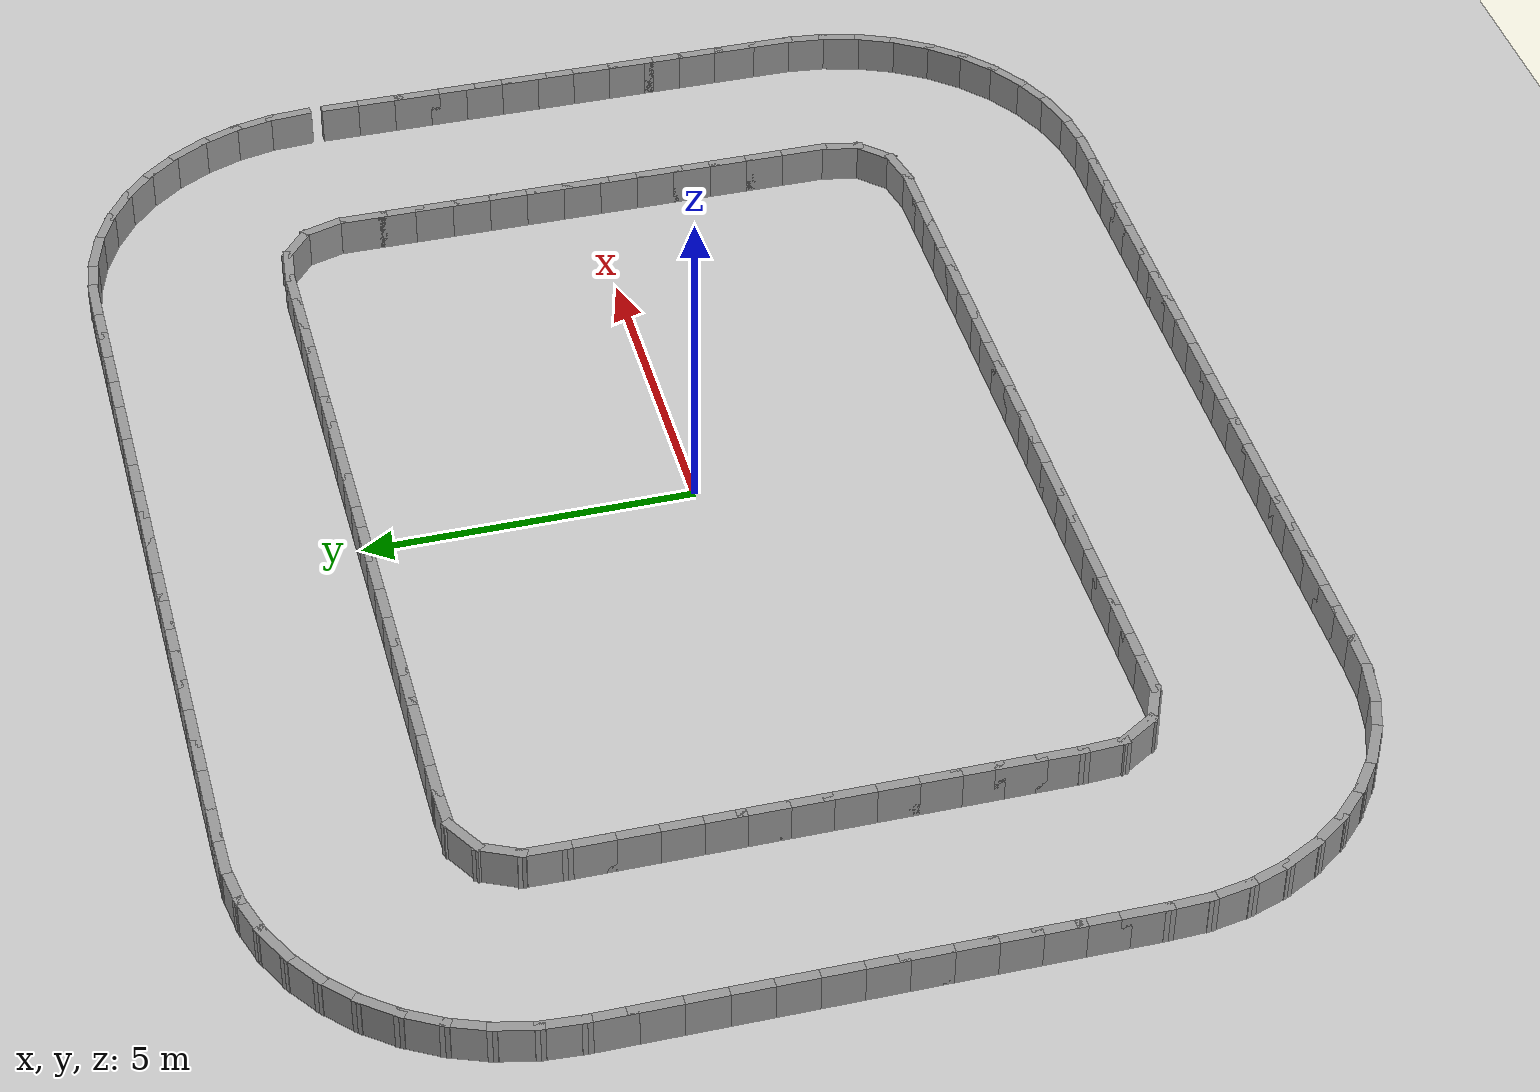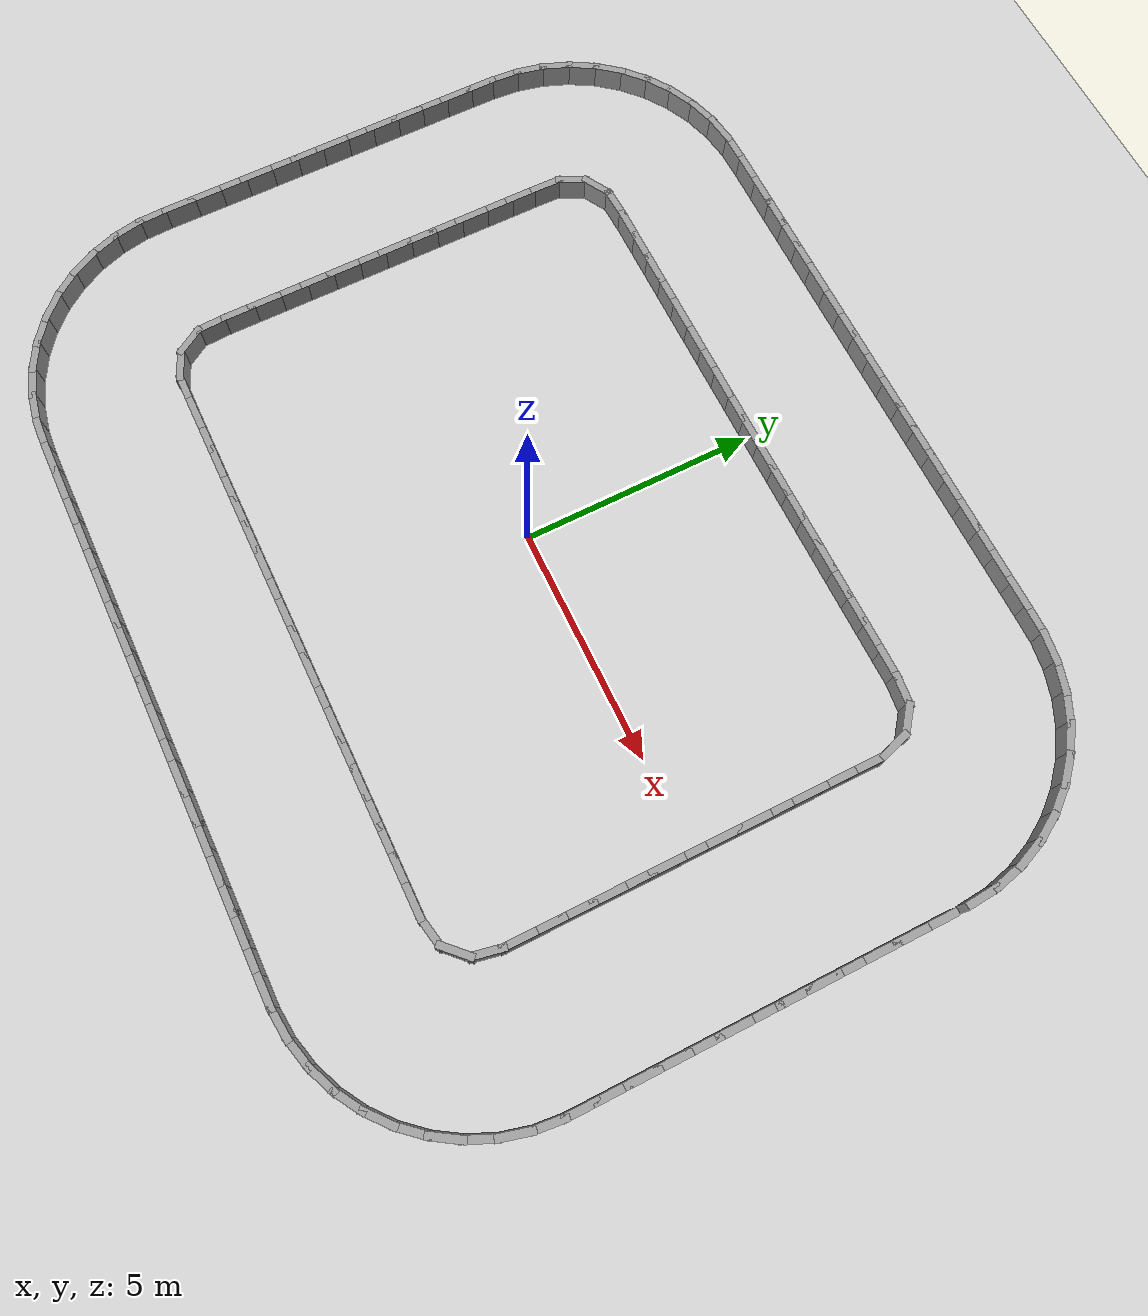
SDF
<?xml version="1.0" ?>
<sdf version='1.7'>
  <world name='default'>
    <plugin name='gazebo_ros_state' filename='libgazebo_ros_state.so'>
      <ros>
        <namespace>/</namespace>
      </ros>
      <update_rate>1000.0</update_rate>
    </plugin>

    <light name='sun' type='directional'>
      <cast_shadows>1</cast_shadows>
      <pose>0 0 10 0 -0 0</pose>
      <diffuse>0.8 0.8 0.8 1</diffuse>
      <specular>0.2 0.2 0.2 1</specular>
      <attenuation>
        <range>1000</range>
        <constant>0.9</constant>
        <linear>0.01</linear>
        <quadratic>0.001</quadratic>
      </attenuation>
      <direction>-0.5 0.1 -0.9</direction>
      <spot>
        <inner_angle>0</inner_angle>
        <outer_angle>0</outer_angle>
        <falloff>0</falloff>
      </spot>
    </light>
    <model name='ground_plane'>
      <static>1</static>
      <link name='link'>
        <collision name='collision'>
          <geometry>
            <plane>
              <normal>0 0 1</normal>
              <size>100 100</size>
            </plane>
          </geometry>
          <surface>
            <friction>
              <ode>
                <mu>100</mu>
                <mu2>50</mu2>
              </ode>
              <torsional>
                <ode/>
              </torsional>
            </friction>
            <contact>
              <ode/>
            </contact>
            <bounce/>
          </surface>
          <max_contacts>10</max_contacts>
        </collision>
        <visual name='visual'>
          <cast_shadows>0</cast_shadows>
          <geometry>
            <plane>
              <normal>0 0 1</normal>
              <size>100 100</size>
            </plane>
          </geometry>
          <material>
            <script>
              <uri>file://media/materials/scripts/gazebo.material</uri>
              <name>Gazebo/Grey</name>
            </script>
          </material>
        </visual>
        <self_collide>0</self_collide>
        <enable_wind>0</enable_wind>
        <kinematic>0</kinematic>
      </link>
    </model>
    <gravity>0 0 -9.8</gravity>
    <magnetic_field>6e-06 2.3e-05 -4.2e-05</magnetic_field>
    <atmosphere type='adiabatic'/>
    <physics type='ode'>
      <max_step_size>0.001</max_step_size>
      <real_time_factor>1</real_time_factor>
      <real_time_update_rate>1000</real_time_update_rate>
    </physics>
    <scene>
      <ambient>0.4 0.4 0.4 1</ambient>
      <background>0.7 0.7 0.7 1</background>
      <shadows>1</shadows>
    </scene>
    <audio>
      <device>default</device>
    </audio>
    <wind/>
    <spherical_coordinates>
      <surface_model>EARTH_WGS84</surface_model>
      <latitude_deg>0</latitude_deg>
      <longitude_deg>0</longitude_deg>
      <elevation>0</elevation>
      <heading_deg>0</heading_deg>
    </spherical_coordinates>
  <model name='parking_lot_loop'>
    <pose>0 0 0 0 -0 0</pose>
    <link name='Wall_0'>
      <collision name='Wall_0_Collision'>
        <geometry><box><size>0.7410 0.1500 0.6000</size></box></geometry>
        <pose>0 0 0.3000 0 -0 0</pose>
      </collision>
      <visual name='Wall_0_Visual'>
        <pose>0 0 0.3000 0 -0 0</pose>
        <geometry><box><size>0.7410 0.1500 0.6000</size></box></geometry>
        <material>
          <script>
            <uri>file://media/materials/scripts/gazebo.material</uri>
            <name>Gazebo/Grey</name>
          </script>
          <ambient>1 1 1 1</ambient>
        </material>
      </visual>
      <pose>6.9127 4.2823 0 0 -0 1.87080</pose>
    </link>
    <link name='Wall_1'>
      <collision name='Wall_1_Collision'>
        <geometry><box><size>0.7410 0.1500 0.6000</size></box></geometry>
        <pose>0 0 0.3000 0 -0 0</pose>
      </collision>
      <visual name='Wall_1_Visual'>
        <pose>0 0 0.3000 0 -0 0</pose>
        <geometry><box><size>0.7410 0.1500 0.6000</size></box></geometry>
        <material>
          <script>
            <uri>file://media/materials/scripts/gazebo.material</uri>
            <name>Gazebo/Grey</name>
          </script>
          <ambient>1 1 1 1</ambient>
        </material>
      </visual>
      <pose>6.5938 4.7483 0 0 -0 2.47079</pose>
    </link>
    <link name='Wall_2'>
      <collision name='Wall_2_Collision'>
        <geometry><box><size>0.7455 0.1500 0.6000</size></box></geometry>
        <pose>0 0 0.3000 0 -0 0</pose>
      </collision>
      <visual name='Wall_2_Visual'>
        <pose>0 0 0.3000 0 -0 0</pose>
        <geometry><box><size>0.7455 0.1500 0.6000</size></box></geometry>
        <material>
          <script>
            <uri>file://media/materials/scripts/gazebo.material</uri>
            <name>Gazebo/Grey</name>
          </script>
          <ambient>1 1 1 1</ambient>
        </material>
      </visual>
      <pose>6.0666 4.9660 0 0 -0 3.02720</pose>
    </link>
    <link name='Wall_3'>
      <collision name='Wall_3_Collision'>
        <geometry><box><size>0.7500 0.1500 0.6000</size></box></geometry>
        <pose>0 0 0.3000 0 -0 0</pose>
      </collision>
      <visual name='Wall_3_Visual'>
        <pose>0 0 0.3000 0 -0 0</pose>
        <geometry><box><size>0.7500 0.1500 0.6000</size></box></geometry>
        <material>
          <script>
            <uri>file://media/materials/scripts/gazebo.material</uri>
            <name>Gazebo/Grey</name>
          </script>
          <ambient>1 1 1 1</ambient>
        </material>
      </visual>
      <pose>5.4708 5.0000 0 0 -0 3.14159</pose>
    </link>
    <link name='Wall_4'>
      <collision name='Wall_4_Collision'>
        <geometry><box><size>0.7500 0.1500 0.6000</size></box></geometry>
        <pose>0 0 0.3000 0 -0 0</pose>
      </collision>
      <visual name='Wall_4_Visual'>
        <pose>0 0 0.3000 0 -0 0</pose>
        <geometry><box><size>0.7500 0.1500 0.6000</size></box></geometry>
        <material>
          <script>
            <uri>file://media/materials/scripts/gazebo.material</uri>
            <name>Gazebo/Grey</name>
          </script>
          <ambient>1 1 1 1</ambient>
        </material>
      </visual>
      <pose>4.8708 5.0000 0 0 -0 3.14159</pose>
    </link>
    <link name='Wall_5'>
      <collision name='Wall_5_Collision'>
        <geometry><box><size>0.7500 0.1500 0.6000</size></box></geometry>
        <pose>0 0 0.3000 0 -0 0</pose>
      </collision>
      <visual name='Wall_5_Visual'>
        <pose>0 0 0.3000 0 -0 0</pose>
        <geometry><box><size>0.7500 0.1500 0.6000</size></box></geometry>
        <material>
          <script>
            <uri>file://media/materials/scripts/gazebo.material</uri>
            <name>Gazebo/Grey</name>
          </script>
          <ambient>1 1 1 1</ambient>
        </material>
      </visual>
      <pose>4.2708 5.0000 0 0 -0 3.14159</pose>
    </link>
    <link name='Wall_6'>
      <collision name='Wall_6_Collision'>
        <geometry><box><size>0.7500 0.1500 0.6000</size></box></geometry>
        <pose>0 0 0.3000 0 -0 0</pose>
      </collision>
      <visual name='Wall_6_Visual'>
        <pose>0 0 0.3000 0 -0 0</pose>
        <geometry><box><size>0.7500 0.1500 0.6000</size></box></geometry>
        <material>
          <script>
            <uri>file://media/materials/scripts/gazebo.material</uri>
            <name>Gazebo/Grey</name>
          </script>
          <ambient>1 1 1 1</ambient>
        </material>
      </visual>
      <pose>3.6708 5.0000 0 0 -0 3.14159</pose>
    </link>
    <link name='Wall_7'>
      <collision name='Wall_7_Collision'>
        <geometry><box><size>0.7500 0.1500 0.6000</size></box></geometry>
        <pose>0 0 0.3000 0 -0 0</pose>
      </collision>
      <visual name='Wall_7_Visual'>
        <pose>0 0 0.3000 0 -0 0</pose>
        <geometry><box><size>0.7500 0.1500 0.6000</size></box></geometry>
        <material>
          <script>
            <uri>file://media/materials/scripts/gazebo.material</uri>
            <name>Gazebo/Grey</name>
          </script>
          <ambient>1 1 1 1</ambient>
        </material>
      </visual>
      <pose>3.0708 5.0000 0 0 -0 3.14159</pose>
    </link>
    <link name='Wall_8'>
      <collision name='Wall_8_Collision'>
        <geometry><box><size>0.7500 0.1500 0.6000</size></box></geometry>
        <pose>0 0 0.3000 0 -0 0</pose>
      </collision>
      <visual name='Wall_8_Visual'>
        <pose>0 0 0.3000 0 -0 0</pose>
        <geometry><box><size>0.7500 0.1500 0.6000</size></box></geometry>
        <material>
          <script>
            <uri>file://media/materials/scripts/gazebo.material</uri>
            <name>Gazebo/Grey</name>
          </script>
          <ambient>1 1 1 1</ambient>
        </material>
      </visual>
      <pose>2.4708 5.0000 0 0 -0 3.14159</pose>
    </link>
    <link name='Wall_9'>
      <collision name='Wall_9_Collision'>
        <geometry><box><size>0.7500 0.1500 0.6000</size></box></geometry>
        <pose>0 0 0.3000 0 -0 0</pose>
      </collision>
      <visual name='Wall_9_Visual'>
        <pose>0 0 0.3000 0 -0 0</pose>
        <geometry><box><size>0.7500 0.1500 0.6000</size></box></geometry>
        <material>
          <script>
            <uri>file://media/materials/scripts/gazebo.material</uri>
            <name>Gazebo/Grey</name>
          </script>
          <ambient>1 1 1 1</ambient>
        </material>
      </visual>
      <pose>1.8708 5.0000 0 0 -0 3.14159</pose>
    </link>
    <link name='Wall_10'>
      <collision name='Wall_10_Collision'>
        <geometry><box><size>0.7500 0.1500 0.6000</size></box></geometry>
        <pose>0 0 0.3000 0 -0 0</pose>
      </collision>
      <visual name='Wall_10_Visual'>
        <pose>0 0 0.3000 0 -0 0</pose>
        <geometry><box><size>0.7500 0.1500 0.6000</size></box></geometry>
        <material>
          <script>
            <uri>file://media/materials/scripts/gazebo.material</uri>
            <name>Gazebo/Grey</name>
          </script>
          <ambient>1 1 1 1</ambient>
        </material>
      </visual>
      <pose>1.2708 5.0000 0 0 -0 3.14159</pose>
    </link>
    <link name='Wall_11'>
      <collision name='Wall_11_Collision'>
        <geometry><box><size>0.7500 0.1500 0.6000</size></box></geometry>
        <pose>0 0 0.3000 0 -0 0</pose>
      </collision>
      <visual name='Wall_11_Visual'>
        <pose>0 0 0.3000 0 -0 0</pose>
        <geometry><box><size>0.7500 0.1500 0.6000</size></box></geometry>
        <material>
          <script>
            <uri>file://media/materials/scripts/gazebo.material</uri>
            <name>Gazebo/Grey</name>
          </script>
          <ambient>1 1 1 1</ambient>
        </material>
      </visual>
      <pose>0.6708 5.0000 0 0 -0 3.14159</pose>
    </link>
    <link name='Wall_12'>
      <collision name='Wall_12_Collision'>
        <geometry><box><size>0.7500 0.1500 0.6000</size></box></geometry>
        <pose>0 0 0.3000 0 -0 0</pose>
      </collision>
      <visual name='Wall_12_Visual'>
        <pose>0 0 0.3000 0 -0 0</pose>
        <geometry><box><size>0.7500 0.1500 0.6000</size></box></geometry>
        <material>
          <script>
            <uri>file://media/materials/scripts/gazebo.material</uri>
            <name>Gazebo/Grey</name>
          </script>
          <ambient>1 1 1 1</ambient>
        </material>
      </visual>
      <pose>0.0708 5.0000 0 0 -0 3.14159</pose>
    </link>
    <link name='Wall_13'>
      <collision name='Wall_13_Collision'>
        <geometry><box><size>0.7500 0.1500 0.6000</size></box></geometry>
        <pose>0 0 0.3000 0 -0 0</pose>
      </collision>
      <visual name='Wall_13_Visual'>
        <pose>0 0 0.3000 0 -0 0</pose>
        <geometry><box><size>0.7500 0.1500 0.6000</size></box></geometry>
        <material>
          <script>
            <uri>file://media/materials/scripts/gazebo.material</uri>
            <name>Gazebo/Grey</name>
          </script>
          <ambient>1 1 1 1</ambient>
        </material>
      </visual>
      <pose>-0.5292 5.0000 0 0 -0 3.14159</pose>
    </link>
    <link name='Wall_14'>
      <collision name='Wall_14_Collision'>
        <geometry><box><size>0.7500 0.1500 0.6000</size></box></geometry>
        <pose>0 0 0.3000 0 -0 0</pose>
      </collision>
      <visual name='Wall_14_Visual'>
        <pose>0 0 0.3000 0 -0 0</pose>
        <geometry><box><size>0.7500 0.1500 0.6000</size></box></geometry>
        <material>
          <script>
            <uri>file://media/materials/scripts/gazebo.material</uri>
            <name>Gazebo/Grey</name>
          </script>
          <ambient>1 1 1 1</ambient>
        </material>
      </visual>
      <pose>-1.1292 5.0000 0 0 -0 3.14159</pose>
    </link>
    <link name='Wall_15'>
      <collision name='Wall_15_Collision'>
        <geometry><box><size>0.7500 0.1500 0.6000</size></box></geometry>
        <pose>0 0 0.3000 0 -0 0</pose>
      </collision>
      <visual name='Wall_15_Visual'>
        <pose>0 0 0.3000 0 -0 0</pose>
        <geometry><box><size>0.7500 0.1500 0.6000</size></box></geometry>
        <material>
          <script>
            <uri>file://media/materials/scripts/gazebo.material</uri>
            <name>Gazebo/Grey</name>
          </script>
          <ambient>1 1 1 1</ambient>
        </material>
      </visual>
      <pose>-1.7292 5.0000 0 0 -0 3.14159</pose>
    </link>
    <link name='Wall_16'>
      <collision name='Wall_16_Collision'>
        <geometry><box><size>0.7500 0.1500 0.6000</size></box></geometry>
        <pose>0 0 0.3000 0 -0 0</pose>
      </collision>
      <visual name='Wall_16_Visual'>
        <pose>0 0 0.3000 0 -0 0</pose>
        <geometry><box><size>0.7500 0.1500 0.6000</size></box></geometry>
        <material>
          <script>
            <uri>file://media/materials/scripts/gazebo.material</uri>
            <name>Gazebo/Grey</name>
          </script>
          <ambient>1 1 1 1</ambient>
        </material>
      </visual>
      <pose>-2.3292 5.0000 0 0 -0 3.14159</pose>
    </link>
    <link name='Wall_17'>
      <collision name='Wall_17_Collision'>
        <geometry><box><size>0.7500 0.1500 0.6000</size></box></geometry>
        <pose>0 0 0.3000 0 -0 0</pose>
      </collision>
      <visual name='Wall_17_Visual'>
        <pose>0 0 0.3000 0 -0 0</pose>
        <geometry><box><size>0.7500 0.1500 0.6000</size></box></geometry>
        <material>
          <script>
            <uri>file://media/materials/scripts/gazebo.material</uri>
            <name>Gazebo/Grey</name>
          </script>
          <ambient>1 1 1 1</ambient>
        </material>
      </visual>
      <pose>-2.9292 5.0000 0 0 -0 3.14159</pose>
    </link>
    <link name='Wall_18'>
      <collision name='Wall_18_Collision'>
        <geometry><box><size>0.7500 0.1500 0.6000</size></box></geometry>
        <pose>0 0 0.3000 0 -0 0</pose>
      </collision>
      <visual name='Wall_18_Visual'>
        <pose>0 0 0.3000 0 -0 0</pose>
        <geometry><box><size>0.7500 0.1500 0.6000</size></box></geometry>
        <material>
          <script>
            <uri>file://media/materials/scripts/gazebo.material</uri>
            <name>Gazebo/Grey</name>
          </script>
          <ambient>1 1 1 1</ambient>
        </material>
      </visual>
      <pose>-3.5292 5.0000 0 0 -0 3.14159</pose>
    </link>
    <link name='Wall_19'>
      <collision name='Wall_19_Collision'>
        <geometry><box><size>0.7500 0.1500 0.6000</size></box></geometry>
        <pose>0 0 0.3000 0 -0 0</pose>
      </collision>
      <visual name='Wall_19_Visual'>
        <pose>0 0 0.3000 0 -0 0</pose>
        <geometry><box><size>0.7500 0.1500 0.6000</size></box></geometry>
        <material>
          <script>
            <uri>file://media/materials/scripts/gazebo.material</uri>
            <name>Gazebo/Grey</name>
          </script>
          <ambient>1 1 1 1</ambient>
        </material>
      </visual>
      <pose>-4.1292 5.0000 0 0 -0 3.14159</pose>
    </link>
    <link name='Wall_20'>
      <collision name='Wall_20_Collision'>
        <geometry><box><size>0.7500 0.1500 0.6000</size></box></geometry>
        <pose>0 0 0.3000 0 -0 0</pose>
      </collision>
      <visual name='Wall_20_Visual'>
        <pose>0 0 0.3000 0 -0 0</pose>
        <geometry><box><size>0.7500 0.1500 0.6000</size></box></geometry>
        <material>
          <script>
            <uri>file://media/materials/scripts/gazebo.material</uri>
            <name>Gazebo/Grey</name>
          </script>
          <ambient>1 1 1 1</ambient>
        </material>
      </visual>
      <pose>-4.7292 5.0000 0 0 -0 3.14159</pose>
    </link>
    <link name='Wall_21'>
      <collision name='Wall_21_Collision'>
        <geometry><box><size>0.7500 0.1500 0.6000</size></box></geometry>
        <pose>0 0 0.3000 0 -0 0</pose>
      </collision>
      <visual name='Wall_21_Visual'>
        <pose>0 0 0.3000 0 -0 0</pose>
        <geometry><box><size>0.7500 0.1500 0.6000</size></box></geometry>
        <material>
          <script>
            <uri>file://media/materials/scripts/gazebo.material</uri>
            <name>Gazebo/Grey</name>
          </script>
          <ambient>1 1 1 1</ambient>
        </material>
      </visual>
      <pose>-5.3292 5.0000 0 0 -0 3.14159</pose>
    </link>
    <link name='Wall_22'>
      <collision name='Wall_22_Collision'>
        <geometry><box><size>0.7486 0.1500 0.6000</size></box></geometry>
        <pose>0 0 0.3000 0 -0 0</pose>
      </collision>
      <visual name='Wall_22_Visual'>
        <pose>0 0 0.3000 0 -0 0</pose>
        <geometry><box><size>0.7486 0.1500 0.6000</size></box></geometry>
        <material>
          <script>
            <uri>file://media/materials/scripts/gazebo.material</uri>
            <name>Gazebo/Grey</name>
          </script>
          <ambient>1 1 1 1</ambient>
        </material>
      </visual>
      <pose>-5.9282 4.9869 0 0 -0 -3.09789</pose>
    </link>
    <link name='Wall_23'>
      <collision name='Wall_23_Collision'>
        <geometry><box><size>0.7410 0.1500 0.6000</size></box></geometry>
        <pose>0 0 0.3000 0 -0 0</pose>
      </collision>
      <visual name='Wall_23_Visual'>
        <pose>0 0 0.3000 0 -0 0</pose>
        <geometry><box><size>0.7410 0.1500 0.6000</size></box></geometry>
        <material>
          <script>
            <uri>file://media/materials/scripts/gazebo.material</uri>
            <name>Gazebo/Grey</name>
          </script>
          <ambient>1 1 1 1</ambient>
        </material>
      </visual>
      <pose>-6.4823 4.8247 0 0 -0 -2.61239</pose>
    </link>
    <link name='Wall_24'>
      <collision name='Wall_24_Collision'>
        <geometry><box><size>0.7410 0.1500 0.6000</size></box></geometry>
        <pose>0 0 0.3000 0 -0 0</pose>
      </collision>
      <visual name='Wall_24_Visual'>
        <pose>0 0 0.3000 0 -0 0</pose>
        <geometry><box><size>0.7410 0.1500 0.6000</size></box></geometry>
        <material>
          <script>
            <uri>file://media/materials/scripts/gazebo.material</uri>
            <name>Gazebo/Grey</name>
          </script>
          <ambient>1 1 1 1</ambient>
        </material>
      </visual>
      <pose>-6.8637 4.4083 0 0 -0 -2.01239</pose>
    </link>
    <link name='Wall_25'>
      <collision name='Wall_25_Collision'>
        <geometry><box><size>0.7496 0.1500 0.6000</size></box></geometry>
        <pose>0 0 0.3000 0 -0 0</pose>
      </collision>
      <visual name='Wall_25_Visual'>
        <pose>0 0 0.3000 0 -0 0</pose>
        <geometry><box><size>0.7496 0.1500 0.6000</size></box></geometry>
        <material>
          <script>
            <uri>file://media/materials/scripts/gazebo.material</uri>
            <name>Gazebo/Grey</name>
          </script>
          <ambient>1 1 1 1</ambient>
        </material>
      </visual>
      <pose>-6.9950 3.8414 0 0 -0 -1.58749</pose>
    </link>
    <link name='Wall_26'>
      <collision name='Wall_26_Collision'>
        <geometry><box><size>0.7500 0.1500 0.6000</size></box></geometry>
        <pose>0 0 0.3000 0 -0 0</pose>
      </collision>
      <visual name='Wall_26_Visual'>
        <pose>0 0 0.3000 0 -0 0</pose>
        <geometry><box><size>0.7500 0.1500 0.6000</size></box></geometry>
        <material>
          <script>
            <uri>file://media/materials/scripts/gazebo.material</uri>
            <name>Gazebo/Grey</name>
          </script>
          <ambient>1 1 1 1</ambient>
        </material>
      </visual>
      <pose>-7.0000 3.2416 0 0 -0 -1.57080</pose>
    </link>
    <link name='Wall_27'>
      <collision name='Wall_27_Collision'>
        <geometry><box><size>0.7500 0.1500 0.6000</size></box></geometry>
        <pose>0 0 0.3000 0 -0 0</pose>
      </collision>
      <visual name='Wall_27_Visual'>
        <pose>0 0 0.3000 0 -0 0</pose>
        <geometry><box><size>0.7500 0.1500 0.6000</size></box></geometry>
        <material>
          <script>
            <uri>file://media/materials/scripts/gazebo.material</uri>
            <name>Gazebo/Grey</name>
          </script>
          <ambient>1 1 1 1</ambient>
        </material>
      </visual>
      <pose>-7.0000 2.6416 0 0 -0 -1.57080</pose>
    </link>
    <link name='Wall_28'>
      <collision name='Wall_28_Collision'>
        <geometry><box><size>0.7500 0.1500 0.6000</size></box></geometry>
        <pose>0 0 0.3000 0 -0 0</pose>
      </collision>
      <visual name='Wall_28_Visual'>
        <pose>0 0 0.3000 0 -0 0</pose>
        <geometry><box><size>0.7500 0.1500 0.6000</size></box></geometry>
        <material>
          <script>
            <uri>file://media/materials/scripts/gazebo.material</uri>
            <name>Gazebo/Grey</name>
          </script>
          <ambient>1 1 1 1</ambient>
        </material>
      </visual>
      <pose>-7.0000 2.0416 0 0 -0 -1.57080</pose>
    </link>
    <link name='Wall_29'>
      <collision name='Wall_29_Collision'>
        <geometry><box><size>0.7500 0.1500 0.6000</size></box></geometry>
        <pose>0 0 0.3000 0 -0 0</pose>
      </collision>
      <visual name='Wall_29_Visual'>
        <pose>0 0 0.3000 0 -0 0</pose>
        <geometry><box><size>0.7500 0.1500 0.6000</size></box></geometry>
        <material>
          <script>
            <uri>file://media/materials/scripts/gazebo.material</uri>
            <name>Gazebo/Grey</name>
          </script>
          <ambient>1 1 1 1</ambient>
        </material>
      </visual>
      <pose>-7.0000 1.4416 0 0 -0 -1.57080</pose>
    </link>
    <link name='Wall_30'>
      <collision name='Wall_30_Collision'>
        <geometry><box><size>0.7500 0.1500 0.6000</size></box></geometry>
        <pose>0 0 0.3000 0 -0 0</pose>
      </collision>
      <visual name='Wall_30_Visual'>
        <pose>0 0 0.3000 0 -0 0</pose>
        <geometry><box><size>0.7500 0.1500 0.6000</size></box></geometry>
        <material>
          <script>
            <uri>file://media/materials/scripts/gazebo.material</uri>
            <name>Gazebo/Grey</name>
          </script>
          <ambient>1 1 1 1</ambient>
        </material>
      </visual>
      <pose>-7.0000 0.8416 0 0 -0 -1.57080</pose>
    </link>
    <link name='Wall_31'>
      <collision name='Wall_31_Collision'>
        <geometry><box><size>0.7500 0.1500 0.6000</size></box></geometry>
        <pose>0 0 0.3000 0 -0 0</pose>
      </collision>
      <visual name='Wall_31_Visual'>
        <pose>0 0 0.3000 0 -0 0</pose>
        <geometry><box><size>0.7500 0.1500 0.6000</size></box></geometry>
        <material>
          <script>
            <uri>file://media/materials/scripts/gazebo.material</uri>
            <name>Gazebo/Grey</name>
          </script>
          <ambient>1 1 1 1</ambient>
        </material>
      </visual>
      <pose>-7.0000 0.2416 0 0 -0 -1.57080</pose>
    </link>
    <link name='Wall_32'>
      <collision name='Wall_32_Collision'>
        <geometry><box><size>0.7500 0.1500 0.6000</size></box></geometry>
        <pose>0 0 0.3000 0 -0 0</pose>
      </collision>
      <visual name='Wall_32_Visual'>
        <pose>0 0 0.3000 0 -0 0</pose>
        <geometry><box><size>0.7500 0.1500 0.6000</size></box></geometry>
        <material>
          <script>
            <uri>file://media/materials/scripts/gazebo.material</uri>
            <name>Gazebo/Grey</name>
          </script>
          <ambient>1 1 1 1</ambient>
        </material>
      </visual>
      <pose>-7.0000 -0.3584 0 0 -0 -1.57080</pose>
    </link>
    <link name='Wall_33'>
      <collision name='Wall_33_Collision'>
        <geometry><box><size>0.7500 0.1500 0.6000</size></box></geometry>
        <pose>0 0 0.3000 0 -0 0</pose>
      </collision>
      <visual name='Wall_33_Visual'>
        <pose>0 0 0.3000 0 -0 0</pose>
        <geometry><box><size>0.7500 0.1500 0.6000</size></box></geometry>
        <material>
          <script>
            <uri>file://media/materials/scripts/gazebo.material</uri>
            <name>Gazebo/Grey</name>
          </script>
          <ambient>1 1 1 1</ambient>
        </material>
      </visual>
      <pose>-7.0000 -0.9584 0 0 -0 -1.57080</pose>
    </link>
    <link name='Wall_34'>
      <collision name='Wall_34_Collision'>
        <geometry><box><size>0.7500 0.1500 0.6000</size></box></geometry>
        <pose>0 0 0.3000 0 -0 0</pose>
      </collision>
      <visual name='Wall_34_Visual'>
        <pose>0 0 0.3000 0 -0 0</pose>
        <geometry><box><size>0.7500 0.1500 0.6000</size></box></geometry>
        <material>
          <script>
            <uri>file://media/materials/scripts/gazebo.material</uri>
            <name>Gazebo/Grey</name>
          </script>
          <ambient>1 1 1 1</ambient>
        </material>
      </visual>
      <pose>-7.0000 -1.5584 0 0 -0 -1.57080</pose>
    </link>
    <link name='Wall_35'>
      <collision name='Wall_35_Collision'>
        <geometry><box><size>0.7500 0.1500 0.6000</size></box></geometry>
        <pose>0 0 0.3000 0 -0 0</pose>
      </collision>
      <visual name='Wall_35_Visual'>
        <pose>0 0 0.3000 0 -0 0</pose>
        <geometry><box><size>0.7500 0.1500 0.6000</size></box></geometry>
        <material>
          <script>
            <uri>file://media/materials/scripts/gazebo.material</uri>
            <name>Gazebo/Grey</name>
          </script>
          <ambient>1 1 1 1</ambient>
        </material>
      </visual>
      <pose>-7.0000 -2.1584 0 0 -0 -1.57080</pose>
    </link>
    <link name='Wall_36'>
      <collision name='Wall_36_Collision'>
        <geometry><box><size>0.7500 0.1500 0.6000</size></box></geometry>
        <pose>0 0 0.3000 0 -0 0</pose>
      </collision>
      <visual name='Wall_36_Visual'>
        <pose>0 0 0.3000 0 -0 0</pose>
        <geometry><box><size>0.7500 0.1500 0.6000</size></box></geometry>
        <material>
          <script>
            <uri>file://media/materials/scripts/gazebo.material</uri>
            <name>Gazebo/Grey</name>
          </script>
          <ambient>1 1 1 1</ambient>
        </material>
      </visual>
      <pose>-7.0000 -2.7584 0 0 -0 -1.57080</pose>
    </link>
    <link name='Wall_37'>
      <collision name='Wall_37_Collision'>
        <geometry><box><size>0.7500 0.1500 0.6000</size></box></geometry>
        <pose>0 0 0.3000 0 -0 0</pose>
      </collision>
      <visual name='Wall_37_Visual'>
        <pose>0 0 0.3000 0 -0 0</pose>
        <geometry><box><size>0.7500 0.1500 0.6000</size></box></geometry>
        <material>
          <script>
            <uri>file://media/materials/scripts/gazebo.material</uri>
            <name>Gazebo/Grey</name>
          </script>
          <ambient>1 1 1 1</ambient>
        </material>
      </visual>
      <pose>-7.0000 -3.3584 0 0 -0 -1.57080</pose>
    </link>
    <link name='Wall_38'>
      <collision name='Wall_38_Collision'>
        <geometry><box><size>0.7481 0.1500 0.6000</size></box></geometry>
        <pose>0 0 0.3000 0 -0 0</pose>
      </collision>
      <visual name='Wall_38_Visual'>
        <pose>0 0 0.3000 0 -0 0</pose>
        <geometry><box><size>0.7481 0.1500 0.6000</size></box></geometry>
        <material>
          <script>
            <uri>file://media/materials/scripts/gazebo.material</uri>
            <name>Gazebo/Grey</name>
          </script>
          <ambient>1 1 1 1</ambient>
        </material>
      </visual>
      <pose>-6.9834 -3.9570 0 0 -0 -1.51525</pose>
    </link>
    <link name='Wall_39'>
      <collision name='Wall_39_Collision'>
        <geometry><box><size>0.7410 0.1500 0.6000</size></box></geometry>
        <pose>0 0 0.3000 0 -0 0</pose>
      </collision>
      <visual name='Wall_39_Visual'>
        <pose>0 0 0.3000 0 -0 0</pose>
        <geometry><box><size>0.7410 0.1500 0.6000</size></box></geometry>
        <material>
          <script>
            <uri>file://media/materials/scripts/gazebo.material</uri>
            <name>Gazebo/Grey</name>
          </script>
          <ambient>1 1 1 1</ambient>
        </material>
      </visual>
      <pose>-6.8102 -4.5062 0 0 -0 -1.01239</pose>
    </link>
    <link name='Wall_40'>
      <collision name='Wall_40_Collision'>
        <geometry><box><size>0.7410 0.1500 0.6000</size></box></geometry>
        <pose>0 0 0.3000 0 -0 0</pose>
      </collision>
      <visual name='Wall_40_Visual'>
        <pose>0 0 0.3000 0 -0 0</pose>
        <geometry><box><size>0.7410 0.1500 0.6000</size></box></geometry>
        <material>
          <script>
            <uri>file://media/materials/scripts/gazebo.material</uri>
            <name>Gazebo/Grey</name>
          </script>
          <ambient>1 1 1 1</ambient>
        </material>
      </visual>
      <pose>-6.3829 -4.8752 0 0 -0 -0.41239</pose>
    </link>
    <link name='Wall_41'>
      <collision name='Wall_41_Collision'>
        <geometry><box><size>0.7498 0.1500 0.6000</size></box></geometry>
        <pose>0 0 0.3000 0 -0 0</pose>
      </collision>
      <visual name='Wall_41_Visual'>
        <pose>0 0 0.3000 0 -0 0</pose>
        <geometry><box><size>0.7498 0.1500 0.6000</size></box></geometry>
        <material>
          <script>
            <uri>file://media/materials/scripts/gazebo.material</uri>
            <name>Gazebo/Grey</name>
          </script>
          <ambient>1 1 1 1</ambient>
        </material>
      </visual>
      <pose>-5.8123 -4.9968 0 0 -0 -0.01052</pose>
    </link>
    <link name='Wall_42'>
      <collision name='Wall_42_Collision'>
        <geometry><box><size>0.7500 0.1500 0.6000</size></box></geometry>
        <pose>0 0 0.3000 0 -0 0</pose>
      </collision>
      <visual name='Wall_42_Visual'>
        <pose>0 0 0.3000 0 -0 0</pose>
        <geometry><box><size>0.7500 0.1500 0.6000</size></box></geometry>
        <material>
          <script>
            <uri>file://media/materials/scripts/gazebo.material</uri>
            <name>Gazebo/Grey</name>
          </script>
          <ambient>1 1 1 1</ambient>
        </material>
      </visual>
      <pose>-5.2124 -5.0000 0 0 -0 0.00000</pose>
    </link>
    <link name='Wall_43'>
      <collision name='Wall_43_Collision'>
        <geometry><box><size>0.7500 0.1500 0.6000</size></box></geometry>
        <pose>0 0 0.3000 0 -0 0</pose>
      </collision>
      <visual name='Wall_43_Visual'>
        <pose>0 0 0.3000 0 -0 0</pose>
        <geometry><box><size>0.7500 0.1500 0.6000</size></box></geometry>
        <material>
          <script>
            <uri>file://media/materials/scripts/gazebo.material</uri>
            <name>Gazebo/Grey</name>
          </script>
          <ambient>1 1 1 1</ambient>
        </material>
      </visual>
      <pose>-4.6124 -5.0000 0 0 -0 0.00000</pose>
    </link>
    <link name='Wall_44'>
      <collision name='Wall_44_Collision'>
        <geometry><box><size>0.7500 0.1500 0.6000</size></box></geometry>
        <pose>0 0 0.3000 0 -0 0</pose>
      </collision>
      <visual name='Wall_44_Visual'>
        <pose>0 0 0.3000 0 -0 0</pose>
        <geometry><box><size>0.7500 0.1500 0.6000</size></box></geometry>
        <material>
          <script>
            <uri>file://media/materials/scripts/gazebo.material</uri>
            <name>Gazebo/Grey</name>
          </script>
          <ambient>1 1 1 1</ambient>
        </material>
      </visual>
      <pose>-4.0124 -5.0000 0 0 -0 0.00000</pose>
    </link>
    <link name='Wall_45'>
      <collision name='Wall_45_Collision'>
        <geometry><box><size>0.7500 0.1500 0.6000</size></box></geometry>
        <pose>0 0 0.3000 0 -0 0</pose>
      </collision>
      <visual name='Wall_45_Visual'>
        <pose>0 0 0.3000 0 -0 0</pose>
        <geometry><box><size>0.7500 0.1500 0.6000</size></box></geometry>
        <material>
          <script>
            <uri>file://media/materials/scripts/gazebo.material</uri>
            <name>Gazebo/Grey</name>
          </script>
          <ambient>1 1 1 1</ambient>
        </material>
      </visual>
      <pose>-3.4124 -5.0000 0 0 -0 0.00000</pose>
    </link>
    <link name='Wall_46'>
      <collision name='Wall_46_Collision'>
        <geometry><box><size>0.7500 0.1500 0.6000</size></box></geometry>
        <pose>0 0 0.3000 0 -0 0</pose>
      </collision>
      <visual name='Wall_46_Visual'>
        <pose>0 0 0.3000 0 -0 0</pose>
        <geometry><box><size>0.7500 0.1500 0.6000</size></box></geometry>
        <material>
          <script>
            <uri>file://media/materials/scripts/gazebo.material</uri>
            <name>Gazebo/Grey</name>
          </script>
          <ambient>1 1 1 1</ambient>
        </material>
      </visual>
      <pose>-2.8124 -5.0000 0 0 -0 0.00000</pose>
    </link>
    <link name='Wall_47'>
      <collision name='Wall_47_Collision'>
        <geometry><box><size>0.7500 0.1500 0.6000</size></box></geometry>
        <pose>0 0 0.3000 0 -0 0</pose>
      </collision>
      <visual name='Wall_47_Visual'>
        <pose>0 0 0.3000 0 -0 0</pose>
        <geometry><box><size>0.7500 0.1500 0.6000</size></box></geometry>
        <material>
          <script>
            <uri>file://media/materials/scripts/gazebo.material</uri>
            <name>Gazebo/Grey</name>
          </script>
          <ambient>1 1 1 1</ambient>
        </material>
      </visual>
      <pose>-2.2124 -5.0000 0 0 -0 0.00000</pose>
    </link>
    <link name='Wall_48'>
      <collision name='Wall_48_Collision'>
        <geometry><box><size>0.7500 0.1500 0.6000</size></box></geometry>
        <pose>0 0 0.3000 0 -0 0</pose>
      </collision>
      <visual name='Wall_48_Visual'>
        <pose>0 0 0.3000 0 -0 0</pose>
        <geometry><box><size>0.7500 0.1500 0.6000</size></box></geometry>
        <material>
          <script>
            <uri>file://media/materials/scripts/gazebo.material</uri>
            <name>Gazebo/Grey</name>
          </script>
          <ambient>1 1 1 1</ambient>
        </material>
      </visual>
      <pose>-1.6124 -5.0000 0 0 -0 0.00000</pose>
    </link>
    <link name='Wall_49'>
      <collision name='Wall_49_Collision'>
        <geometry><box><size>0.7500 0.1500 0.6000</size></box></geometry>
        <pose>0 0 0.3000 0 -0 0</pose>
      </collision>
      <visual name='Wall_49_Visual'>
        <pose>0 0 0.3000 0 -0 0</pose>
        <geometry><box><size>0.7500 0.1500 0.6000</size></box></geometry>
        <material>
          <script>
            <uri>file://media/materials/scripts/gazebo.material</uri>
            <name>Gazebo/Grey</name>
          </script>
          <ambient>1 1 1 1</ambient>
        </material>
      </visual>
      <pose>-1.0124 -5.0000 0 0 -0 0.00000</pose>
    </link>
    <link name='Wall_50'>
      <collision name='Wall_50_Collision'>
        <geometry><box><size>0.7500 0.1500 0.6000</size></box></geometry>
        <pose>0 0 0.3000 0 -0 0</pose>
      </collision>
      <visual name='Wall_50_Visual'>
        <pose>0 0 0.3000 0 -0 0</pose>
        <geometry><box><size>0.7500 0.1500 0.6000</size></box></geometry>
        <material>
          <script>
            <uri>file://media/materials/scripts/gazebo.material</uri>
            <name>Gazebo/Grey</name>
          </script>
          <ambient>1 1 1 1</ambient>
        </material>
      </visual>
      <pose>-0.4124 -5.0000 0 0 -0 0.00000</pose>
    </link>
    <link name='Wall_51'>
      <collision name='Wall_51_Collision'>
        <geometry><box><size>0.7500 0.1500 0.6000</size></box></geometry>
        <pose>0 0 0.3000 0 -0 0</pose>
      </collision>
      <visual name='Wall_51_Visual'>
        <pose>0 0 0.3000 0 -0 0</pose>
        <geometry><box><size>0.7500 0.1500 0.6000</size></box></geometry>
        <material>
          <script>
            <uri>file://media/materials/scripts/gazebo.material</uri>
            <name>Gazebo/Grey</name>
          </script>
          <ambient>1 1 1 1</ambient>
        </material>
      </visual>
      <pose>0.1876 -5.0000 0 0 -0 0.00000</pose>
    </link>
    <link name='Wall_52'>
      <collision name='Wall_52_Collision'>
        <geometry><box><size>0.7500 0.1500 0.6000</size></box></geometry>
        <pose>0 0 0.3000 0 -0 0</pose>
      </collision>
      <visual name='Wall_52_Visual'>
        <pose>0 0 0.3000 0 -0 0</pose>
        <geometry><box><size>0.7500 0.1500 0.6000</size></box></geometry>
        <material>
          <script>
            <uri>file://media/materials/scripts/gazebo.material</uri>
            <name>Gazebo/Grey</name>
          </script>
          <ambient>1 1 1 1</ambient>
        </material>
      </visual>
      <pose>0.7876 -5.0000 0 0 -0 0.00000</pose>
    </link>
    <link name='Wall_53'>
      <collision name='Wall_53_Collision'>
        <geometry><box><size>0.7500 0.1500 0.6000</size></box></geometry>
        <pose>0 0 0.3000 0 -0 0</pose>
      </collision>
      <visual name='Wall_53_Visual'>
        <pose>0 0 0.3000 0 -0 0</pose>
        <geometry><box><size>0.7500 0.1500 0.6000</size></box></geometry>
        <material>
          <script>
            <uri>file://media/materials/scripts/gazebo.material</uri>
            <name>Gazebo/Grey</name>
          </script>
          <ambient>1 1 1 1</ambient>
        </material>
      </visual>
      <pose>1.3876 -5.0000 0 0 -0 0.00000</pose>
    </link>
    <link name='Wall_54'>
      <collision name='Wall_54_Collision'>
        <geometry><box><size>0.7500 0.1500 0.6000</size></box></geometry>
        <pose>0 0 0.3000 0 -0 0</pose>
      </collision>
      <visual name='Wall_54_Visual'>
        <pose>0 0 0.3000 0 -0 0</pose>
        <geometry><box><size>0.7500 0.1500 0.6000</size></box></geometry>
        <material>
          <script>
            <uri>file://media/materials/scripts/gazebo.material</uri>
            <name>Gazebo/Grey</name>
          </script>
          <ambient>1 1 1 1</ambient>
        </material>
      </visual>
      <pose>1.9876 -5.0000 0 0 -0 0.00000</pose>
    </link>
    <link name='Wall_55'>
      <collision name='Wall_55_Collision'>
        <geometry><box><size>0.7500 0.1500 0.6000</size></box></geometry>
        <pose>0 0 0.3000 0 -0 0</pose>
      </collision>
      <visual name='Wall_55_Visual'>
        <pose>0 0 0.3000 0 -0 0</pose>
        <geometry><box><size>0.7500 0.1500 0.6000</size></box></geometry>
        <material>
          <script>
            <uri>file://media/materials/scripts/gazebo.material</uri>
            <name>Gazebo/Grey</name>
          </script>
          <ambient>1 1 1 1</ambient>
        </material>
      </visual>
      <pose>2.5876 -5.0000 0 0 -0 0.00000</pose>
    </link>
    <link name='Wall_56'>
      <collision name='Wall_56_Collision'>
        <geometry><box><size>0.7500 0.1500 0.6000</size></box></geometry>
        <pose>0 0 0.3000 0 -0 0</pose>
      </collision>
      <visual name='Wall_56_Visual'>
        <pose>0 0 0.3000 0 -0 0</pose>
        <geometry><box><size>0.7500 0.1500 0.6000</size></box></geometry>
        <material>
          <script>
            <uri>file://media/materials/scripts/gazebo.material</uri>
            <name>Gazebo/Grey</name>
          </script>
          <ambient>1 1 1 1</ambient>
        </material>
      </visual>
      <pose>3.1876 -5.0000 0 0 -0 0.00000</pose>
    </link>
    <link name='Wall_57'>
      <collision name='Wall_57_Collision'>
        <geometry><box><size>0.7500 0.1500 0.6000</size></box></geometry>
        <pose>0 0 0.3000 0 -0 0</pose>
      </collision>
      <visual name='Wall_57_Visual'>
        <pose>0 0 0.3000 0 -0 0</pose>
        <geometry><box><size>0.7500 0.1500 0.6000</size></box></geometry>
        <material>
          <script>
            <uri>file://media/materials/scripts/gazebo.material</uri>
            <name>Gazebo/Grey</name>
          </script>
          <ambient>1 1 1 1</ambient>
        </material>
      </visual>
      <pose>3.7876 -5.0000 0 0 -0 0.00000</pose>
    </link>
    <link name='Wall_58'>
      <collision name='Wall_58_Collision'>
        <geometry><box><size>0.7500 0.1500 0.6000</size></box></geometry>
        <pose>0 0 0.3000 0 -0 0</pose>
      </collision>
      <visual name='Wall_58_Visual'>
        <pose>0 0 0.3000 0 -0 0</pose>
        <geometry><box><size>0.7500 0.1500 0.6000</size></box></geometry>
        <material>
          <script>
            <uri>file://media/materials/scripts/gazebo.material</uri>
            <name>Gazebo/Grey</name>
          </script>
          <ambient>1 1 1 1</ambient>
        </material>
      </visual>
      <pose>4.3876 -5.0000 0 0 -0 0.00000</pose>
    </link>
    <link name='Wall_59'>
      <collision name='Wall_59_Collision'>
        <geometry><box><size>0.7500 0.1500 0.6000</size></box></geometry>
        <pose>0 0 0.3000 0 -0 0</pose>
      </collision>
      <visual name='Wall_59_Visual'>
        <pose>0 0 0.3000 0 -0 0</pose>
        <geometry><box><size>0.7500 0.1500 0.6000</size></box></geometry>
        <material>
          <script>
            <uri>file://media/materials/scripts/gazebo.material</uri>
            <name>Gazebo/Grey</name>
          </script>
          <ambient>1 1 1 1</ambient>
        </material>
      </visual>
      <pose>4.9876 -5.0000 0 0 -0 0.00000</pose>
    </link>
    <link name='Wall_60'>
      <collision name='Wall_60_Collision'>
        <geometry><box><size>0.7500 0.1500 0.6000</size></box></geometry>
        <pose>0 0 0.3000 0 -0 0</pose>
      </collision>
      <visual name='Wall_60_Visual'>
        <pose>0 0 0.3000 0 -0 0</pose>
        <geometry><box><size>0.7500 0.1500 0.6000</size></box></geometry>
        <material>
          <script>
            <uri>file://media/materials/scripts/gazebo.material</uri>
            <name>Gazebo/Grey</name>
          </script>
          <ambient>1 1 1 1</ambient>
        </material>
      </visual>
      <pose>5.5876 -5.0000 0 0 -0 0.00000</pose>
    </link>
    <link name='Wall_61'>
      <collision name='Wall_61_Collision'>
        <geometry><box><size>0.7425 0.1500 0.6000</size></box></geometry>
        <pose>0 0 0.3000 0 -0 0</pose>
      </collision>
      <visual name='Wall_61_Visual'>
        <pose>0 0 0.3000 0 -0 0</pose>
        <geometry><box><size>0.7425 0.1500 0.6000</size></box></geometry>
        <material>
          <script>
            <uri>file://media/materials/scripts/gazebo.material</uri>
            <name>Gazebo/Grey</name>
          </script>
          <ambient>1 1 1 1</ambient>
        </material>
      </visual>
      <pose>6.1781 -4.9417 0 0 -0 0.19800</pose>
    </link>
    <link name='Wall_62'>
      <collision name='Wall_62_Collision'>
        <geometry><box><size>0.7410 0.1500 0.6000</size></box></geometry>
        <pose>0 0 0.3000 0 -0 0</pose>
      </collision>
      <visual name='Wall_62_Visual'>
        <pose>0 0 0.3000 0 -0 0</pose>
        <geometry><box><size>0.7410 0.1500 0.6000</size></box></geometry>
        <material>
          <script>
            <uri>file://media/materials/scripts/gazebo.material</uri>
            <name>Gazebo/Grey</name>
          </script>
          <ambient>1 1 1 1</ambient>
        </material>
      </visual>
      <pose>6.6770 -4.6740 0 0 -0 0.78761</pose>
    </link>
    <link name='Wall_63'>
      <collision name='Wall_63_Collision'>
        <geometry><box><size>0.7426 0.1500 0.6000</size></box></geometry>
        <pose>0 0 0.3000 0 -0 0</pose>
      </collision>
      <visual name='Wall_63_Visual'>
        <pose>0 0 0.3000 0 -0 0</pose>
        <geometry><box><size>0.7426 0.1500 0.6000</size></box></geometry>
        <material>
          <script>
            <uri>file://media/materials/scripts/gazebo.material</uri>
            <name>Gazebo/Grey</name>
          </script>
          <ambient>1 1 1 1</ambient>
        </material>
      </visual>
      <pose>6.9428 -4.1739 0 0 -0 1.37638</pose>
    </link>
    <link name='Wall_64'>
      <collision name='Wall_64_Collision'>
        <geometry><box><size>0.7500 0.1500 0.6000</size></box></geometry>
        <pose>0 0 0.3000 0 -0 0</pose>
      </collision>
      <visual name='Wall_64_Visual'>
        <pose>0 0 0.3000 0 -0 0</pose>
        <geometry><box><size>0.7500 0.1500 0.6000</size></box></geometry>
        <material>
          <script>
            <uri>file://media/materials/scripts/gazebo.material</uri>
            <name>Gazebo/Grey</name>
          </script>
          <ambient>1 1 1 1</ambient>
        </material>
      </visual>
      <pose>7.0000 -3.5832 0 0 -0 1.57080</pose>
    </link>
    <link name='Wall_65'>
      <collision name='Wall_65_Collision'>
        <geometry><box><size>0.7500 0.1500 0.6000</size></box></geometry>
        <pose>0 0 0.3000 0 -0 0</pose>
      </collision>
      <visual name='Wall_65_Visual'>
        <pose>0 0 0.3000 0 -0 0</pose>
        <geometry><box><size>0.7500 0.1500 0.6000</size></box></geometry>
        <material>
          <script>
            <uri>file://media/materials/scripts/gazebo.material</uri>
            <name>Gazebo/Grey</name>
          </script>
          <ambient>1 1 1 1</ambient>
        </material>
      </visual>
      <pose>7.0000 -2.9832 0 0 -0 1.57080</pose>
    </link>
    <link name='Wall_66'>
      <collision name='Wall_66_Collision'>
        <geometry><box><size>0.7500 0.1500 0.6000</size></box></geometry>
        <pose>0 0 0.3000 0 -0 0</pose>
      </collision>
      <visual name='Wall_66_Visual'>
        <pose>0 0 0.3000 0 -0 0</pose>
        <geometry><box><size>0.7500 0.1500 0.6000</size></box></geometry>
        <material>
          <script>
            <uri>file://media/materials/scripts/gazebo.material</uri>
            <name>Gazebo/Grey</name>
          </script>
          <ambient>1 1 1 1</ambient>
        </material>
      </visual>
      <pose>7.0000 -2.3832 0 0 -0 1.57080</pose>
    </link>
    <link name='Wall_67'>
      <collision name='Wall_67_Collision'>
        <geometry><box><size>0.7500 0.1500 0.6000</size></box></geometry>
        <pose>0 0 0.3000 0 -0 0</pose>
      </collision>
      <visual name='Wall_67_Visual'>
        <pose>0 0 0.3000 0 -0 0</pose>
        <geometry><box><size>0.7500 0.1500 0.6000</size></box></geometry>
        <material>
          <script>
            <uri>file://media/materials/scripts/gazebo.material</uri>
            <name>Gazebo/Grey</name>
          </script>
          <ambient>1 1 1 1</ambient>
        </material>
      </visual>
      <pose>7.0000 -1.7832 0 0 -0 1.57080</pose>
    </link>
    <link name='Wall_68'>
      <collision name='Wall_68_Collision'>
        <geometry><box><size>0.7500 0.1500 0.6000</size></box></geometry>
        <pose>0 0 0.3000 0 -0 0</pose>
      </collision>
      <visual name='Wall_68_Visual'>
        <pose>0 0 0.3000 0 -0 0</pose>
        <geometry><box><size>0.7500 0.1500 0.6000</size></box></geometry>
        <material>
          <script>
            <uri>file://media/materials/scripts/gazebo.material</uri>
            <name>Gazebo/Grey</name>
          </script>
          <ambient>1 1 1 1</ambient>
        </material>
      </visual>
      <pose>7.0000 -1.1832 0 0 -0 1.57080</pose>
    </link>
    <link name='Wall_69'>
      <collision name='Wall_69_Collision'>
        <geometry><box><size>0.7500 0.1500 0.6000</size></box></geometry>
        <pose>0 0 0.3000 0 -0 0</pose>
      </collision>
      <visual name='Wall_69_Visual'>
        <pose>0 0 0.3000 0 -0 0</pose>
        <geometry><box><size>0.7500 0.1500 0.6000</size></box></geometry>
        <material>
          <script>
            <uri>file://media/materials/scripts/gazebo.material</uri>
            <name>Gazebo/Grey</name>
          </script>
          <ambient>1 1 1 1</ambient>
        </material>
      </visual>
      <pose>7.0000 -0.5832 0 0 -0 1.57080</pose>
    </link>
    <link name='Wall_70'>
      <collision name='Wall_70_Collision'>
        <geometry><box><size>0.7500 0.1500 0.6000</size></box></geometry>
        <pose>0 0 0.3000 0 -0 0</pose>
      </collision>
      <visual name='Wall_70_Visual'>
        <pose>0 0 0.3000 0 -0 0</pose>
        <geometry><box><size>0.7500 0.1500 0.6000</size></box></geometry>
        <material>
          <script>
            <uri>file://media/materials/scripts/gazebo.material</uri>
            <name>Gazebo/Grey</name>
          </script>
          <ambient>1 1 1 1</ambient>
        </material>
      </visual>
      <pose>7.0000 0.0168 0 0 -0 1.57080</pose>
    </link>
    <link name='Wall_71'>
      <collision name='Wall_71_Collision'>
        <geometry><box><size>0.7500 0.1500 0.6000</size></box></geometry>
        <pose>0 0 0.3000 0 -0 0</pose>
      </collision>
      <visual name='Wall_71_Visual'>
        <pose>0 0 0.3000 0 -0 0</pose>
        <geometry><box><size>0.7500 0.1500 0.6000</size></box></geometry>
        <material>
          <script>
            <uri>file://media/materials/scripts/gazebo.material</uri>
            <name>Gazebo/Grey</name>
          </script>
          <ambient>1 1 1 1</ambient>
        </material>
      </visual>
      <pose>7.0000 0.6168 0 0 -0 1.57080</pose>
    </link>
    <link name='Wall_72'>
      <collision name='Wall_72_Collision'>
        <geometry><box><size>0.7500 0.1500 0.6000</size></box></geometry>
        <pose>0 0 0.3000 0 -0 0</pose>
      </collision>
      <visual name='Wall_72_Visual'>
        <pose>0 0 0.3000 0 -0 0</pose>
        <geometry><box><size>0.7500 0.1500 0.6000</size></box></geometry>
        <material>
          <script>
            <uri>file://media/materials/scripts/gazebo.material</uri>
            <name>Gazebo/Grey</name>
          </script>
          <ambient>1 1 1 1</ambient>
        </material>
      </visual>
      <pose>7.0000 1.2168 0 0 -0 1.57080</pose>
    </link>
    <link name='Wall_73'>
      <collision name='Wall_73_Collision'>
        <geometry><box><size>0.7500 0.1500 0.6000</size></box></geometry>
        <pose>0 0 0.3000 0 -0 0</pose>
      </collision>
      <visual name='Wall_73_Visual'>
        <pose>0 0 0.3000 0 -0 0</pose>
        <geometry><box><size>0.7500 0.1500 0.6000</size></box></geometry>
        <material>
          <script>
            <uri>file://media/materials/scripts/gazebo.material</uri>
            <name>Gazebo/Grey</name>
          </script>
          <ambient>1 1 1 1</ambient>
        </material>
      </visual>
      <pose>7.0000 1.8168 0 0 -0 1.57080</pose>
    </link>
    <link name='Wall_74'>
      <collision name='Wall_74_Collision'>
        <geometry><box><size>0.7500 0.1500 0.6000</size></box></geometry>
        <pose>0 0 0.3000 0 -0 0</pose>
      </collision>
      <visual name='Wall_74_Visual'>
        <pose>0 0 0.3000 0 -0 0</pose>
        <geometry><box><size>0.7500 0.1500 0.6000</size></box></geometry>
        <material>
          <script>
            <uri>file://media/materials/scripts/gazebo.material</uri>
            <name>Gazebo/Grey</name>
          </script>
          <ambient>1 1 1 1</ambient>
        </material>
      </visual>
      <pose>7.0000 2.4168 0 0 -0 1.57080</pose>
    </link>
    <link name='Wall_75'>
      <collision name='Wall_75_Collision'>
        <geometry><box><size>0.7500 0.1500 0.6000</size></box></geometry>
        <pose>0 0 0.3000 0 -0 0</pose>
      </collision>
      <visual name='Wall_75_Visual'>
        <pose>0 0 0.3000 0 -0 0</pose>
        <geometry><box><size>0.7500 0.1500 0.6000</size></box></geometry>
        <material>
          <script>
            <uri>file://media/materials/scripts/gazebo.material</uri>
            <name>Gazebo/Grey</name>
          </script>
          <ambient>1 1 1 1</ambient>
        </material>
      </visual>
      <pose>7.0000 3.0168 0 0 -0 1.57080</pose>
    </link>
    <link name='Wall_76'>
      <collision name='Wall_76_Collision'>
        <geometry><box><size>0.7500 0.1500 0.6000</size></box></geometry>
        <pose>0 0 0.3000 0 -0 0</pose>
      </collision>
      <visual name='Wall_76_Visual'>
        <pose>0 0 0.3000 0 -0 0</pose>
        <geometry><box><size>0.7500 0.1500 0.6000</size></box></geometry>
        <material>
          <script>
            <uri>file://media/materials/scripts/gazebo.material</uri>
            <name>Gazebo/Grey</name>
          </script>
          <ambient>1 1 1 1</ambient>
        </material>
      </visual>
      <pose>7.0000 3.6168 0 0 -0 1.57080</pose>
    </link>
    <link name='Wall_77'>
      <collision name='Wall_77_Collision'>
        <geometry><box><size>0.7494 0.1500 0.6000</size></box></geometry>
        <pose>0 0 0.3000 0 -0 0</pose>
      </collision>
      <visual name='Wall_77_Visual'>
        <pose>0 0 0.3000 0 -0 0</pose>
        <geometry><box><size>0.7494 0.1500 0.6000</size></box></geometry>
        <material>
          <script>
            <uri>file://media/materials/scripts/gazebo.material</uri>
            <name>Gazebo/Grey</name>
          </script>
          <ambient>1 1 1 1</ambient>
        </material>
      </visual>
      <pose>9.9775 4.2989 0 0 -0 1.64581</pose>
    </link>
    <link name='Wall_78'>
      <collision name='Wall_78_Collision'>
        <geometry><box><size>0.7494 0.1500 0.6000</size></box></geometry>
        <pose>0 0 0.3000 0 -0 0</pose>
      </collision>
      <visual name='Wall_78_Visual'>
        <pose>0 0 0.3000 0 -0 0</pose>
        <geometry><box><size>0.7494 0.1500 0.6000</size></box></geometry>
        <material>
          <script>
            <uri>file://media/materials/scripts/gazebo.material</uri>
            <name>Gazebo/Grey</name>
          </script>
          <ambient>1 1 1 1</ambient>
        </material>
      </visual>
      <pose>9.8882 4.8899 0 0 -0 1.79580</pose>
    </link>
    <link name='Wall_79'>
      <collision name='Wall_79_Collision'>
        <geometry><box><size>0.7494 0.1500 0.6000</size></box></geometry>
        <pose>0 0 0.3000 0 -0 0</pose>
      </collision>
      <visual name='Wall_79_Visual'>
        <pose>0 0 0.3000 0 -0 0</pose>
        <geometry><box><size>0.7494 0.1500 0.6000</size></box></geometry>
        <material>
          <script>
            <uri>file://media/materials/scripts/gazebo.material</uri>
            <name>Gazebo/Grey</name>
          </script>
          <ambient>1 1 1 1</ambient>
        </material>
      </visual>
      <pose>9.7116 5.4610 0 0 -0 1.94578</pose>
    </link>
    <link name='Wall_80'>
      <collision name='Wall_80_Collision'>
        <geometry><box><size>0.7494 0.1500 0.6000</size></box></geometry>
        <pose>0 0 0.3000 0 -0 0</pose>
      </collision>
      <visual name='Wall_80_Visual'>
        <pose>0 0 0.3000 0 -0 0</pose>
        <geometry><box><size>0.7494 0.1500 0.6000</size></box></geometry>
        <material>
          <script>
            <uri>file://media/materials/scripts/gazebo.material</uri>
            <name>Gazebo/Grey</name>
          </script>
          <ambient>1 1 1 1</ambient>
        </material>
      </visual>
      <pose>9.4516 5.9992 0 0 -0 2.09581</pose>
    </link>
    <link name='Wall_81'>
      <collision name='Wall_81_Collision'>
        <geometry><box><size>0.7494 0.1500 0.6000</size></box></geometry>
        <pose>0 0 0.3000 0 -0 0</pose>
      </collision>
      <visual name='Wall_81_Visual'>
        <pose>0 0 0.3000 0 -0 0</pose>
        <geometry><box><size>0.7494 0.1500 0.6000</size></box></geometry>
        <material>
          <script>
            <uri>file://media/materials/scripts/gazebo.material</uri>
            <name>Gazebo/Grey</name>
          </script>
          <ambient>1 1 1 1</ambient>
        </material>
      </visual>
      <pose>9.1140 6.4926 0 0 -0 2.24580</pose>
    </link>
    <link name='Wall_82'>
      <collision name='Wall_82_Collision'>
        <geometry><box><size>0.7494 0.1500 0.6000</size></box></geometry>
        <pose>0 0 0.3000 0 -0 0</pose>
      </collision>
      <visual name='Wall_82_Visual'>
        <pose>0 0 0.3000 0 -0 0</pose>
        <geometry><box><size>0.7494 0.1500 0.6000</size></box></geometry>
        <material>
          <script>
            <uri>file://media/materials/scripts/gazebo.material</uri>
            <name>Gazebo/Grey</name>
          </script>
          <ambient>1 1 1 1</ambient>
        </material>
      </visual>
      <pose>8.7066 6.9299 0 0 -0 2.39579</pose>
    </link>
    <link name='Wall_83'>
      <collision name='Wall_83_Collision'>
        <geometry><box><size>0.7494 0.1500 0.6000</size></box></geometry>
        <pose>0 0 0.3000 0 -0 0</pose>
      </collision>
      <visual name='Wall_83_Visual'>
        <pose>0 0 0.3000 0 -0 0</pose>
        <geometry><box><size>0.7494 0.1500 0.6000</size></box></geometry>
        <material>
          <script>
            <uri>file://media/materials/scripts/gazebo.material</uri>
            <name>Gazebo/Grey</name>
          </script>
          <ambient>1 1 1 1</ambient>
        </material>
      </visual>
      <pose>8.2384 7.3015 0 0 -0 2.54581</pose>
    </link>
    <link name='Wall_84'>
      <collision name='Wall_84_Collision'>
        <geometry><box><size>0.7494 0.1500 0.6000</size></box></geometry>
        <pose>0 0 0.3000 0 -0 0</pose>
      </collision>
      <visual name='Wall_84_Visual'>
        <pose>0 0 0.3000 0 -0 0</pose>
        <geometry><box><size>0.7494 0.1500 0.6000</size></box></geometry>
        <material>
          <script>
            <uri>file://media/materials/scripts/gazebo.material</uri>
            <name>Gazebo/Grey</name>
          </script>
          <ambient>1 1 1 1</ambient>
        </material>
      </visual>
      <pose>7.7198 7.5989 0 0 -0 2.69580</pose>
    </link>
    <link name='Wall_85'>
      <collision name='Wall_85_Collision'>
        <geometry><box><size>0.7494 0.1500 0.6000</size></box></geometry>
        <pose>0 0 0.3000 0 -0 0</pose>
      </collision>
      <visual name='Wall_85_Visual'>
        <pose>0 0 0.3000 0 -0 0</pose>
        <geometry><box><size>0.7494 0.1500 0.6000</size></box></geometry>
        <material>
          <script>
            <uri>file://media/materials/scripts/gazebo.material</uri>
            <name>Gazebo/Grey</name>
          </script>
          <ambient>1 1 1 1</ambient>
        </material>
      </visual>
      <pose>7.1627 7.8155 0 0 -0 2.84579</pose>
    </link>
    <link name='Wall_86'>
      <collision name='Wall_86_Collision'>
        <geometry><box><size>0.7494 0.1500 0.6000</size></box></geometry>
        <pose>0 0 0.3000 0 -0 0</pose>
      </collision>
      <visual name='Wall_86_Visual'>
        <pose>0 0 0.3000 0 -0 0</pose>
        <geometry><box><size>0.7494 0.1500 0.6000</size></box></geometry>
        <material>
          <script>
            <uri>file://media/materials/scripts/gazebo.material</uri>
            <name>Gazebo/Grey</name>
          </script>
          <ambient>1 1 1 1</ambient>
        </material>
      </visual>
      <pose>6.5795 7.9464 0 0 -0 2.99581</pose>
    </link>
    <link name='Wall_87'>
      <collision name='Wall_87_Collision'>
        <geometry><box><size>0.7498 0.1500 0.6000</size></box></geometry>
        <pose>0 0 0.3000 0 -0 0</pose>
      </collision>
      <visual name='Wall_87_Visual'>
        <pose>0 0 0.3000 0 -0 0</pose>
        <geometry><box><size>0.7498 0.1500 0.6000</size></box></geometry>
        <material>
          <script>
            <uri>file://media/materials/scripts/gazebo.material</uri>
            <name>Gazebo/Grey</name>
          </script>
          <ambient>1 1 1 1</ambient>
        </material>
      </visual>
      <pose>5.9831 7.9950 0 0 -0 3.12488</pose>
    </link>
    <link name='Wall_88'>
      <collision name='Wall_88_Collision'>
        <geometry><box><size>0.7500 0.1500 0.6000</size></box></geometry>
        <pose>0 0 0.3000 0 -0 0</pose>
      </collision>
      <visual name='Wall_88_Visual'>
        <pose>0 0 0.3000 0 -0 0</pose>
        <geometry><box><size>0.7500 0.1500 0.6000</size></box></geometry>
        <material>
          <script>
            <uri>file://media/materials/scripts/gazebo.material</uri>
            <name>Gazebo/Grey</name>
          </script>
          <ambient>1 1 1 1</ambient>
        </material>
      </visual>
      <pose>5.3832 8.0000 0 0 -0 3.14159</pose>
    </link>
    <link name='Wall_89'>
      <collision name='Wall_89_Collision'>
        <geometry><box><size>0.7500 0.1500 0.6000</size></box></geometry>
        <pose>0 0 0.3000 0 -0 0</pose>
      </collision>
      <visual name='Wall_89_Visual'>
        <pose>0 0 0.3000 0 -0 0</pose>
        <geometry><box><size>0.7500 0.1500 0.6000</size></box></geometry>
        <material>
          <script>
            <uri>file://media/materials/scripts/gazebo.material</uri>
            <name>Gazebo/Grey</name>
          </script>
          <ambient>1 1 1 1</ambient>
        </material>
      </visual>
      <pose>4.7832 8.0000 0 0 -0 3.14159</pose>
    </link>
    <link name='Wall_90'>
      <collision name='Wall_90_Collision'>
        <geometry><box><size>0.7500 0.1500 0.6000</size></box></geometry>
        <pose>0 0 0.3000 0 -0 0</pose>
      </collision>
      <visual name='Wall_90_Visual'>
        <pose>0 0 0.3000 0 -0 0</pose>
        <geometry><box><size>0.7500 0.1500 0.6000</size></box></geometry>
        <material>
          <script>
            <uri>file://media/materials/scripts/gazebo.material</uri>
            <name>Gazebo/Grey</name>
          </script>
          <ambient>1 1 1 1</ambient>
        </material>
      </visual>
      <pose>4.1832 8.0000 0 0 -0 3.14159</pose>
    </link>
    <link name='Wall_91'>
      <collision name='Wall_91_Collision'>
        <geometry><box><size>0.7500 0.1500 0.6000</size></box></geometry>
        <pose>0 0 0.3000 0 -0 0</pose>
      </collision>
      <visual name='Wall_91_Visual'>
        <pose>0 0 0.3000 0 -0 0</pose>
        <geometry><box><size>0.7500 0.1500 0.6000</size></box></geometry>
        <material>
          <script>
            <uri>file://media/materials/scripts/gazebo.material</uri>
            <name>Gazebo/Grey</name>
          </script>
          <ambient>1 1 1 1</ambient>
        </material>
      </visual>
      <pose>3.5832 8.0000 0 0 -0 3.14159</pose>
    </link>
    <link name='Wall_92'>
      <collision name='Wall_92_Collision'>
        <geometry><box><size>0.7500 0.1500 0.6000</size></box></geometry>
        <pose>0 0 0.3000 0 -0 0</pose>
      </collision>
      <visual name='Wall_92_Visual'>
        <pose>0 0 0.3000 0 -0 0</pose>
        <geometry><box><size>0.7500 0.1500 0.6000</size></box></geometry>
        <material>
          <script>
            <uri>file://media/materials/scripts/gazebo.material</uri>
            <name>Gazebo/Grey</name>
          </script>
          <ambient>1 1 1 1</ambient>
        </material>
      </visual>
      <pose>2.9832 8.0000 0 0 -0 3.14159</pose>
    </link>
    <link name='Wall_93'>
      <collision name='Wall_93_Collision'>
        <geometry><box><size>0.7500 0.1500 0.6000</size></box></geometry>
        <pose>0 0 0.3000 0 -0 0</pose>
      </collision>
      <visual name='Wall_93_Visual'>
        <pose>0 0 0.3000 0 -0 0</pose>
        <geometry><box><size>0.7500 0.1500 0.6000</size></box></geometry>
        <material>
          <script>
            <uri>file://media/materials/scripts/gazebo.material</uri>
            <name>Gazebo/Grey</name>
          </script>
          <ambient>1 1 1 1</ambient>
        </material>
      </visual>
      <pose>2.3832 8.0000 0 0 -0 3.14159</pose>
    </link>
    <link name='Wall_94'>
      <collision name='Wall_94_Collision'>
        <geometry><box><size>0.7500 0.1500 0.6000</size></box></geometry>
        <pose>0 0 0.3000 0 -0 0</pose>
      </collision>
      <visual name='Wall_94_Visual'>
        <pose>0 0 0.3000 0 -0 0</pose>
        <geometry><box><size>0.7500 0.1500 0.6000</size></box></geometry>
        <material>
          <script>
            <uri>file://media/materials/scripts/gazebo.material</uri>
            <name>Gazebo/Grey</name>
          </script>
          <ambient>1 1 1 1</ambient>
        </material>
      </visual>
      <pose>1.7832 8.0000 0 0 -0 3.14159</pose>
    </link>
    <link name='Wall_95'>
      <collision name='Wall_95_Collision'>
        <geometry><box><size>0.7500 0.1500 0.6000</size></box></geometry>
        <pose>0 0 0.3000 0 -0 0</pose>
      </collision>
      <visual name='Wall_95_Visual'>
        <pose>0 0 0.3000 0 -0 0</pose>
        <geometry><box><size>0.7500 0.1500 0.6000</size></box></geometry>
        <material>
          <script>
            <uri>file://media/materials/scripts/gazebo.material</uri>
            <name>Gazebo/Grey</name>
          </script>
          <ambient>1 1 1 1</ambient>
        </material>
      </visual>
      <pose>1.1832 8.0000 0 0 -0 3.14159</pose>
    </link>
    <link name='Wall_96'>
      <collision name='Wall_96_Collision'>
        <geometry><box><size>0.7500 0.1500 0.6000</size></box></geometry>
        <pose>0 0 0.3000 0 -0 0</pose>
      </collision>
      <visual name='Wall_96_Visual'>
        <pose>0 0 0.3000 0 -0 0</pose>
        <geometry><box><size>0.7500 0.1500 0.6000</size></box></geometry>
        <material>
          <script>
            <uri>file://media/materials/scripts/gazebo.material</uri>
            <name>Gazebo/Grey</name>
          </script>
          <ambient>1 1 1 1</ambient>
        </material>
      </visual>
      <pose>0.5832 8.0000 0 0 -0 3.14159</pose>
    </link>
    <link name='Wall_97'>
      <collision name='Wall_97_Collision'>
        <geometry><box><size>0.7500 0.1500 0.6000</size></box></geometry>
        <pose>0 0 0.3000 0 -0 0</pose>
      </collision>
      <visual name='Wall_97_Visual'>
        <pose>0 0 0.3000 0 -0 0</pose>
        <geometry><box><size>0.7500 0.1500 0.6000</size></box></geometry>
        <material>
          <script>
            <uri>file://media/materials/scripts/gazebo.material</uri>
            <name>Gazebo/Grey</name>
          </script>
          <ambient>1 1 1 1</ambient>
        </material>
      </visual>
      <pose>-0.0168 8.0000 0 0 -0 3.14159</pose>
    </link>
    <link name='Wall_98'>
      <collision name='Wall_98_Collision'>
        <geometry><box><size>0.7500 0.1500 0.6000</size></box></geometry>
        <pose>0 0 0.3000 0 -0 0</pose>
      </collision>
      <visual name='Wall_98_Visual'>
        <pose>0 0 0.3000 0 -0 0</pose>
        <geometry><box><size>0.7500 0.1500 0.6000</size></box></geometry>
        <material>
          <script>
            <uri>file://media/materials/scripts/gazebo.material</uri>
            <name>Gazebo/Grey</name>
          </script>
          <ambient>1 1 1 1</ambient>
        </material>
      </visual>
      <pose>-0.6168 8.0000 0 0 -0 3.14159</pose>
    </link>
    <link name='Wall_99'>
      <collision name='Wall_99_Collision'>
        <geometry><box><size>0.7500 0.1500 0.6000</size></box></geometry>
        <pose>0 0 0.3000 0 -0 0</pose>
      </collision>
      <visual name='Wall_99_Visual'>
        <pose>0 0 0.3000 0 -0 0</pose>
        <geometry><box><size>0.7500 0.1500 0.6000</size></box></geometry>
        <material>
          <script>
            <uri>file://media/materials/scripts/gazebo.material</uri>
            <name>Gazebo/Grey</name>
          </script>
          <ambient>1 1 1 1</ambient>
        </material>
      </visual>
      <pose>-1.2168 8.0000 0 0 -0 3.14159</pose>
    </link>
    <link name='Wall_100'>
      <collision name='Wall_100_Collision'>
        <geometry><box><size>0.7500 0.1500 0.6000</size></box></geometry>
        <pose>0 0 0.3000 0 -0 0</pose>
      </collision>
      <visual name='Wall_100_Visual'>
        <pose>0 0 0.3000 0 -0 0</pose>
        <geometry><box><size>0.7500 0.1500 0.6000</size></box></geometry>
        <material>
          <script>
            <uri>file://media/materials/scripts/gazebo.material</uri>
            <name>Gazebo/Grey</name>
          </script>
          <ambient>1 1 1 1</ambient>
        </material>
      </visual>
      <pose>-1.8168 8.0000 0 0 -0 3.14159</pose>
    </link>
    <link name='Wall_101'>
      <collision name='Wall_101_Collision'>
        <geometry><box><size>0.7500 0.1500 0.6000</size></box></geometry>
        <pose>0 0 0.3000 0 -0 0</pose>
      </collision>
      <visual name='Wall_101_Visual'>
        <pose>0 0 0.3000 0 -0 0</pose>
        <geometry><box><size>0.7500 0.1500 0.6000</size></box></geometry>
        <material>
          <script>
            <uri>file://media/materials/scripts/gazebo.material</uri>
            <name>Gazebo/Grey</name>
          </script>
          <ambient>1 1 1 1</ambient>
        </material>
      </visual>
      <pose>-2.4168 8.0000 0 0 -0 3.14159</pose>
    </link>
    <link name='Wall_102'>
      <collision name='Wall_102_Collision'>
        <geometry><box><size>0.7500 0.1500 0.6000</size></box></geometry>
        <pose>0 0 0.3000 0 -0 0</pose>
      </collision>
      <visual name='Wall_102_Visual'>
        <pose>0 0 0.3000 0 -0 0</pose>
        <geometry><box><size>0.7500 0.1500 0.6000</size></box></geometry>
        <material>
          <script>
            <uri>file://media/materials/scripts/gazebo.material</uri>
            <name>Gazebo/Grey</name>
          </script>
          <ambient>1 1 1 1</ambient>
        </material>
      </visual>
      <pose>-3.0168 8.0000 0 0 -0 3.14159</pose>
    </link>
    <link name='Wall_103'>
      <collision name='Wall_103_Collision'>
        <geometry><box><size>0.7500 0.1500 0.6000</size></box></geometry>
        <pose>0 0 0.3000 0 -0 0</pose>
      </collision>
      <visual name='Wall_103_Visual'>
        <pose>0 0 0.3000 0 -0 0</pose>
        <geometry><box><size>0.7500 0.1500 0.6000</size></box></geometry>
        <material>
          <script>
            <uri>file://media/materials/scripts/gazebo.material</uri>
            <name>Gazebo/Grey</name>
          </script>
          <ambient>1 1 1 1</ambient>
        </material>
      </visual>
      <pose>-3.6168 8.0000 0 0 -0 3.14159</pose>
    </link>
    <link name='Wall_104'>
      <collision name='Wall_104_Collision'>
        <geometry><box><size>0.7500 0.1500 0.6000</size></box></geometry>
        <pose>0 0 0.3000 0 -0 0</pose>
      </collision>
      <visual name='Wall_104_Visual'>
        <pose>0 0 0.3000 0 -0 0</pose>
        <geometry><box><size>0.7500 0.1500 0.6000</size></box></geometry>
        <material>
          <script>
            <uri>file://media/materials/scripts/gazebo.material</uri>
            <name>Gazebo/Grey</name>
          </script>
          <ambient>1 1 1 1</ambient>
        </material>
      </visual>
      <pose>-4.2168 8.0000 0 0 -0 3.14159</pose>
    </link>
    <link name='Wall_105'>
      <collision name='Wall_105_Collision'>
        <geometry><box><size>0.7500 0.1500 0.6000</size></box></geometry>
        <pose>0 0 0.3000 0 -0 0</pose>
      </collision>
      <visual name='Wall_105_Visual'>
        <pose>0 0 0.3000 0 -0 0</pose>
        <geometry><box><size>0.7500 0.1500 0.6000</size></box></geometry>
        <material>
          <script>
            <uri>file://media/materials/scripts/gazebo.material</uri>
            <name>Gazebo/Grey</name>
          </script>
          <ambient>1 1 1 1</ambient>
        </material>
      </visual>
      <pose>-4.8168 8.0000 0 0 -0 3.14159</pose>
    </link>
    <link name='Wall_106'>
      <collision name='Wall_106_Collision'>
        <geometry><box><size>0.7500 0.1500 0.6000</size></box></geometry>
        <pose>0 0 0.3000 0 -0 0</pose>
      </collision>
      <visual name='Wall_106_Visual'>
        <pose>0 0 0.3000 0 -0 0</pose>
        <geometry><box><size>0.7500 0.1500 0.6000</size></box></geometry>
        <material>
          <script>
            <uri>file://media/materials/scripts/gazebo.material</uri>
            <name>Gazebo/Grey</name>
          </script>
          <ambient>1 1 1 1</ambient>
        </material>
      </visual>
      <pose>-5.4168 8.0000 0 0 -0 3.14159</pose>
    </link>
    <link name='Wall_107'>
      <collision name='Wall_107_Collision'>
        <geometry><box><size>0.7498 0.1500 0.6000</size></box></geometry>
        <pose>0 0 0.3000 0 -0 0</pose>
      </collision>
      <visual name='Wall_107_Visual'>
        <pose>0 0 0.3000 0 -0 0</pose>
        <geometry><box><size>0.7498 0.1500 0.6000</size></box></geometry>
        <material>
          <script>
            <uri>file://media/materials/scripts/gazebo.material</uri>
            <name>Gazebo/Grey</name>
          </script>
          <ambient>1 1 1 1</ambient>
        </material>
      </visual>
      <pose>-6.0167 7.9937 0 0 -0 -3.12067</pose>
    </link>
    <link name='Wall_108'>
      <collision name='Wall_108_Collision'>
        <geometry><box><size>0.7494 0.1500 0.6000</size></box></geometry>
        <pose>0 0 0.3000 0 -0 0</pose>
      </collision>
      <visual name='Wall_108_Visual'>
        <pose>0 0 0.3000 0 -0 0</pose>
        <geometry><box><size>0.7494 0.1500 0.6000</size></box></geometry>
        <material>
          <script>
            <uri>file://media/materials/scripts/gazebo.material</uri>
            <name>Gazebo/Grey</name>
          </script>
          <ambient>1 1 1 1</ambient>
        </material>
      </visual>
      <pose>-6.6127 7.9414 0 0 -0 -2.98740</pose>
    </link>
    <link name='Wall_109'>
      <collision name='Wall_109_Collision'>
        <geometry><box><size>0.7494 0.1500 0.6000</size></box></geometry>
        <pose>0 0 0.3000 0 -0 0</pose>
      </collision>
      <visual name='Wall_109_Visual'>
        <pose>0 0 0.3000 0 -0 0</pose>
        <geometry><box><size>0.7494 0.1500 0.6000</size></box></geometry>
        <material>
          <script>
            <uri>file://media/materials/scripts/gazebo.material</uri>
            <name>Gazebo/Grey</name>
          </script>
          <ambient>1 1 1 1</ambient>
        </material>
      </visual>
      <pose>-7.1948 7.8056 0 0 -0 -2.83738</pose>
    </link>
    <link name='Wall_110'>
      <collision name='Wall_110_Collision'>
        <geometry><box><size>0.7494 0.1500 0.6000</size></box></geometry>
        <pose>0 0 0.3000 0 -0 0</pose>
      </collision>
      <visual name='Wall_110_Visual'>
        <pose>0 0 0.3000 0 -0 0</pose>
        <geometry><box><size>0.7494 0.1500 0.6000</size></box></geometry>
        <material>
          <script>
            <uri>file://media/materials/scripts/gazebo.material</uri>
            <name>Gazebo/Grey</name>
          </script>
          <ambient>1 1 1 1</ambient>
        </material>
      </visual>
      <pose>-7.7501 7.5843 0 0 -0 -2.68738</pose>
    </link>
    <link name='Wall_111'>
      <collision name='Wall_111_Collision'>
        <geometry><box><size>0.7494 0.1500 0.6000</size></box></geometry>
        <pose>0 0 0.3000 0 -0 0</pose>
      </collision>
      <visual name='Wall_111_Visual'>
        <pose>0 0 0.3000 0 -0 0</pose>
        <geometry><box><size>0.7494 0.1500 0.6000</size></box></geometry>
        <material>
          <script>
            <uri>file://media/materials/scripts/gazebo.material</uri>
            <name>Gazebo/Grey</name>
          </script>
          <ambient>1 1 1 1</ambient>
        </material>
      </visual>
      <pose>-8.2660 7.2826 0 0 -0 -2.53740</pose>
    </link>
    <link name='Wall_112'>
      <collision name='Wall_112_Collision'>
        <geometry><box><size>0.7494 0.1500 0.6000</size></box></geometry>
        <pose>0 0 0.3000 0 -0 0</pose>
      </collision>
      <visual name='Wall_112_Visual'>
        <pose>0 0 0.3000 0 -0 0</pose>
        <geometry><box><size>0.7494 0.1500 0.6000</size></box></geometry>
        <material>
          <script>
            <uri>file://media/materials/scripts/gazebo.material</uri>
            <name>Gazebo/Grey</name>
          </script>
          <ambient>1 1 1 1</ambient>
        </material>
      </visual>
      <pose>-8.7311 6.9071 0 0 -0 -2.38738</pose>
    </link>
    <link name='Wall_113'>
      <collision name='Wall_113_Collision'>
        <geometry><box><size>0.7494 0.1500 0.6000</size></box></geometry>
        <pose>0 0 0.3000 0 -0 0</pose>
      </collision>
      <visual name='Wall_113_Visual'>
        <pose>0 0 0.3000 0 -0 0</pose>
        <geometry><box><size>0.7494 0.1500 0.6000</size></box></geometry>
        <material>
          <script>
            <uri>file://media/materials/scripts/gazebo.material</uri>
            <name>Gazebo/Grey</name>
          </script>
          <ambient>1 1 1 1</ambient>
        </material>
      </visual>
      <pose>-9.1349 6.4663 0 0 -0 -2.23738</pose>
    </link>
    <link name='Wall_114'>
      <collision name='Wall_114_Collision'>
        <geometry><box><size>0.7494 0.1500 0.6000</size></box></geometry>
        <pose>0 0 0.3000 0 -0 0</pose>
      </collision>
      <visual name='Wall_114_Visual'>
        <pose>0 0 0.3000 0 -0 0</pose>
        <geometry><box><size>0.7494 0.1500 0.6000</size></box></geometry>
        <material>
          <script>
            <uri>file://media/materials/scripts/gazebo.material</uri>
            <name>Gazebo/Grey</name>
          </script>
          <ambient>1 1 1 1</ambient>
        </material>
      </visual>
      <pose>-9.4683 5.9701 0 0 -0 -2.08740</pose>
    </link>
    <link name='Wall_115'>
      <collision name='Wall_115_Collision'>
        <geometry><box><size>0.7494 0.1500 0.6000</size></box></geometry>
        <pose>0 0 0.3000 0 -0 0</pose>
      </collision>
      <visual name='Wall_115_Visual'>
        <pose>0 0 0.3000 0 -0 0</pose>
        <geometry><box><size>0.7494 0.1500 0.6000</size></box></geometry>
        <material>
          <script>
            <uri>file://media/materials/scripts/gazebo.material</uri>
            <name>Gazebo/Grey</name>
          </script>
          <ambient>1 1 1 1</ambient>
        </material>
      </visual>
      <pose>-9.7237 5.4297 0 0 -0 -1.93738</pose>
    </link>
    <link name='Wall_116'>
      <collision name='Wall_116_Collision'>
        <geometry><box><size>0.7494 0.1500 0.6000</size></box></geometry>
        <pose>0 0 0.3000 0 -0 0</pose>
      </collision>
      <visual name='Wall_116_Visual'>
        <pose>0 0 0.3000 0 -0 0</pose>
        <geometry><box><size>0.7494 0.1500 0.6000</size></box></geometry>
        <material>
          <script>
            <uri>file://media/materials/scripts/gazebo.material</uri>
            <name>Gazebo/Grey</name>
          </script>
          <ambient>1 1 1 1</ambient>
        </material>
      </visual>
      <pose>-9.8956 4.8572 0 0 -0 -1.78738</pose>
    </link>
    <link name='Wall_117'>
      <collision name='Wall_117_Collision'>
        <geometry><box><size>0.7494 0.1500 0.6000</size></box></geometry>
        <pose>0 0 0.3000 0 -0 0</pose>
      </collision>
      <visual name='Wall_117_Visual'>
        <pose>0 0 0.3000 0 -0 0</pose>
        <geometry><box><size>0.7494 0.1500 0.6000</size></box></geometry>
        <material>
          <script>
            <uri>file://media/materials/scripts/gazebo.material</uri>
            <name>Gazebo/Grey</name>
          </script>
          <ambient>1 1 1 1</ambient>
        </material>
      </visual>
      <pose>-9.9800 4.2654 0 0 -0 -1.63764</pose>
    </link>
    <link name='Wall_118'>
      <collision name='Wall_118_Collision'>
        <geometry><box><size>0.7500 0.1500 0.6000</size></box></geometry>
        <pose>0 0 0.3000 0 -0 0</pose>
      </collision>
      <visual name='Wall_118_Visual'>
        <pose>0 0 0.3000 0 -0 0</pose>
        <geometry><box><size>0.7500 0.1500 0.6000</size></box></geometry>
        <material>
          <script>
            <uri>file://media/materials/scripts/gazebo.material</uri>
            <name>Gazebo/Grey</name>
          </script>
          <ambient>1 1 1 1</ambient>
        </material>
      </visual>
      <pose>-10.0000 3.6664 0 0 -0 -1.57080</pose>
    </link>
    <link name='Wall_119'>
      <collision name='Wall_119_Collision'>
        <geometry><box><size>0.7500 0.1500 0.6000</size></box></geometry>
        <pose>0 0 0.3000 0 -0 0</pose>
      </collision>
      <visual name='Wall_119_Visual'>
        <pose>0 0 0.3000 0 -0 0</pose>
        <geometry><box><size>0.7500 0.1500 0.6000</size></box></geometry>
        <material>
          <script>
            <uri>file://media/materials/scripts/gazebo.material</uri>
            <name>Gazebo/Grey</name>
          </script>
          <ambient>1 1 1 1</ambient>
        </material>
      </visual>
      <pose>-10.0000 3.0664 0 0 -0 -1.57080</pose>
    </link>
    <link name='Wall_120'>
      <collision name='Wall_120_Collision'>
        <geometry><box><size>0.7500 0.1500 0.6000</size></box></geometry>
        <pose>0 0 0.3000 0 -0 0</pose>
      </collision>
      <visual name='Wall_120_Visual'>
        <pose>0 0 0.3000 0 -0 0</pose>
        <geometry><box><size>0.7500 0.1500 0.6000</size></box></geometry>
        <material>
          <script>
            <uri>file://media/materials/scripts/gazebo.material</uri>
            <name>Gazebo/Grey</name>
          </script>
          <ambient>1 1 1 1</ambient>
        </material>
      </visual>
      <pose>-10.0000 2.4664 0 0 -0 -1.57080</pose>
    </link>
    <link name='Wall_121'>
      <collision name='Wall_121_Collision'>
        <geometry><box><size>0.7500 0.1500 0.6000</size></box></geometry>
        <pose>0 0 0.3000 0 -0 0</pose>
      </collision>
      <visual name='Wall_121_Visual'>
        <pose>0 0 0.3000 0 -0 0</pose>
        <geometry><box><size>0.7500 0.1500 0.6000</size></box></geometry>
        <material>
          <script>
            <uri>file://media/materials/scripts/gazebo.material</uri>
            <name>Gazebo/Grey</name>
          </script>
          <ambient>1 1 1 1</ambient>
        </material>
      </visual>
      <pose>-10.0000 1.8664 0 0 -0 -1.57080</pose>
    </link>
    <link name='Wall_122'>
      <collision name='Wall_122_Collision'>
        <geometry><box><size>0.7500 0.1500 0.6000</size></box></geometry>
        <pose>0 0 0.3000 0 -0 0</pose>
      </collision>
      <visual name='Wall_122_Visual'>
        <pose>0 0 0.3000 0 -0 0</pose>
        <geometry><box><size>0.7500 0.1500 0.6000</size></box></geometry>
        <material>
          <script>
            <uri>file://media/materials/scripts/gazebo.material</uri>
            <name>Gazebo/Grey</name>
          </script>
          <ambient>1 1 1 1</ambient>
        </material>
      </visual>
      <pose>-10.0000 1.2664 0 0 -0 -1.57080</pose>
    </link>
    <link name='Wall_123'>
      <collision name='Wall_123_Collision'>
        <geometry><box><size>0.7500 0.1500 0.6000</size></box></geometry>
        <pose>0 0 0.3000 0 -0 0</pose>
      </collision>
      <visual name='Wall_123_Visual'>
        <pose>0 0 0.3000 0 -0 0</pose>
        <geometry><box><size>0.7500 0.1500 0.6000</size></box></geometry>
        <material>
          <script>
            <uri>file://media/materials/scripts/gazebo.material</uri>
            <name>Gazebo/Grey</name>
          </script>
          <ambient>1 1 1 1</ambient>
        </material>
      </visual>
      <pose>-10.0000 0.6664 0 0 -0 -1.57080</pose>
    </link>
    <link name='Wall_124'>
      <collision name='Wall_124_Collision'>
        <geometry><box><size>0.7500 0.1500 0.6000</size></box></geometry>
        <pose>0 0 0.3000 0 -0 0</pose>
      </collision>
      <visual name='Wall_124_Visual'>
        <pose>0 0 0.3000 0 -0 0</pose>
        <geometry><box><size>0.7500 0.1500 0.6000</size></box></geometry>
        <material>
          <script>
            <uri>file://media/materials/scripts/gazebo.material</uri>
            <name>Gazebo/Grey</name>
          </script>
          <ambient>1 1 1 1</ambient>
        </material>
      </visual>
      <pose>-10.0000 0.0664 0 0 -0 -1.57080</pose>
    </link>
    <link name='Wall_125'>
      <collision name='Wall_125_Collision'>
        <geometry><box><size>0.7500 0.1500 0.6000</size></box></geometry>
        <pose>0 0 0.3000 0 -0 0</pose>
      </collision>
      <visual name='Wall_125_Visual'>
        <pose>0 0 0.3000 0 -0 0</pose>
        <geometry><box><size>0.7500 0.1500 0.6000</size></box></geometry>
        <material>
          <script>
            <uri>file://media/materials/scripts/gazebo.material</uri>
            <name>Gazebo/Grey</name>
          </script>
          <ambient>1 1 1 1</ambient>
        </material>
      </visual>
      <pose>-10.0000 -0.5336 0 0 -0 -1.57080</pose>
    </link>
    <link name='Wall_126'>
      <collision name='Wall_126_Collision'>
        <geometry><box><size>0.7500 0.1500 0.6000</size></box></geometry>
        <pose>0 0 0.3000 0 -0 0</pose>
      </collision>
      <visual name='Wall_126_Visual'>
        <pose>0 0 0.3000 0 -0 0</pose>
        <geometry><box><size>0.7500 0.1500 0.6000</size></box></geometry>
        <material>
          <script>
            <uri>file://media/materials/scripts/gazebo.material</uri>
            <name>Gazebo/Grey</name>
          </script>
          <ambient>1 1 1 1</ambient>
        </material>
      </visual>
      <pose>-10.0000 -1.1336 0 0 -0 -1.57080</pose>
    </link>
    <link name='Wall_127'>
      <collision name='Wall_127_Collision'>
        <geometry><box><size>0.7500 0.1500 0.6000</size></box></geometry>
        <pose>0 0 0.3000 0 -0 0</pose>
      </collision>
      <visual name='Wall_127_Visual'>
        <pose>0 0 0.3000 0 -0 0</pose>
        <geometry><box><size>0.7500 0.1500 0.6000</size></box></geometry>
        <material>
          <script>
            <uri>file://media/materials/scripts/gazebo.material</uri>
            <name>Gazebo/Grey</name>
          </script>
          <ambient>1 1 1 1</ambient>
        </material>
      </visual>
      <pose>-10.0000 -1.7336 0 0 -0 -1.57080</pose>
    </link>
    <link name='Wall_128'>
      <collision name='Wall_128_Collision'>
        <geometry><box><size>0.7500 0.1500 0.6000</size></box></geometry>
        <pose>0 0 0.3000 0 -0 0</pose>
      </collision>
      <visual name='Wall_128_Visual'>
        <pose>0 0 0.3000 0 -0 0</pose>
        <geometry><box><size>0.7500 0.1500 0.6000</size></box></geometry>
        <material>
          <script>
            <uri>file://media/materials/scripts/gazebo.material</uri>
            <name>Gazebo/Grey</name>
          </script>
          <ambient>1 1 1 1</ambient>
        </material>
      </visual>
      <pose>-10.0000 -2.3336 0 0 -0 -1.57080</pose>
    </link>
    <link name='Wall_129'>
      <collision name='Wall_129_Collision'>
        <geometry><box><size>0.7500 0.1500 0.6000</size></box></geometry>
        <pose>0 0 0.3000 0 -0 0</pose>
      </collision>
      <visual name='Wall_129_Visual'>
        <pose>0 0 0.3000 0 -0 0</pose>
        <geometry><box><size>0.7500 0.1500 0.6000</size></box></geometry>
        <material>
          <script>
            <uri>file://media/materials/scripts/gazebo.material</uri>
            <name>Gazebo/Grey</name>
          </script>
          <ambient>1 1 1 1</ambient>
        </material>
      </visual>
      <pose>-10.0000 -2.9336 0 0 -0 -1.57080</pose>
    </link>
    <link name='Wall_130'>
      <collision name='Wall_130_Collision'>
        <geometry><box><size>0.7500 0.1500 0.6000</size></box></geometry>
        <pose>0 0 0.3000 0 -0 0</pose>
      </collision>
      <visual name='Wall_130_Visual'>
        <pose>0 0 0.3000 0 -0 0</pose>
        <geometry><box><size>0.7500 0.1500 0.6000</size></box></geometry>
        <material>
          <script>
            <uri>file://media/materials/scripts/gazebo.material</uri>
            <name>Gazebo/Grey</name>
          </script>
          <ambient>1 1 1 1</ambient>
        </material>
      </visual>
      <pose>-10.0000 -3.5336 0 0 -0 -1.57080</pose>
    </link>
    <link name='Wall_131'>
      <collision name='Wall_131_Collision'>
        <geometry><box><size>0.7496 0.1500 0.6000</size></box></geometry>
        <pose>0 0 0.3000 0 -0 0</pose>
      </collision>
      <visual name='Wall_131_Visual'>
        <pose>0 0 0.3000 0 -0 0</pose>
        <geometry><box><size>0.7496 0.1500 0.6000</size></box></geometry>
        <material>
          <script>
            <uri>file://media/materials/scripts/gazebo.material</uri>
            <name>Gazebo/Grey</name>
          </script>
          <ambient>1 1 1 1</ambient>
        </material>
      </visual>
      <pose>-9.9883 -4.1332 0 0 -0 -1.53162</pose>
    </link>
    <link name='Wall_132'>
      <collision name='Wall_132_Collision'>
        <geometry><box><size>0.7494 0.1500 0.6000</size></box></geometry>
        <pose>0 0 0.3000 0 -0 0</pose>
      </collision>
      <visual name='Wall_132_Visual'>
        <pose>0 0 0.3000 0 -0 0</pose>
        <geometry><box><size>0.7494 0.1500 0.6000</size></box></geometry>
        <material>
          <script>
            <uri>file://media/materials/scripts/gazebo.material</uri>
            <name>Gazebo/Grey</name>
          </script>
          <ambient>1 1 1 1</ambient>
        </material>
      </visual>
      <pose>-9.9218 -4.7275 0 0 -0 -1.38737</pose>
    </link>
    <link name='Wall_133'>
      <collision name='Wall_133_Collision'>
        <geometry><box><size>0.7494 0.1500 0.6000</size></box></geometry>
        <pose>0 0 0.3000 0 -0 0</pose>
      </collision>
      <visual name='Wall_133_Visual'>
        <pose>0 0 0.3000 0 -0 0</pose>
        <geometry><box><size>0.7494 0.1500 0.6000</size></box></geometry>
        <material>
          <script>
            <uri>file://media/materials/scripts/gazebo.material</uri>
            <name>Gazebo/Grey</name>
          </script>
          <ambient>1 1 1 1</ambient>
        </material>
      </visual>
      <pose>-9.7691 -5.3054 0 0 -0 -1.23739</pose>
    </link>
    <link name='Wall_134'>
      <collision name='Wall_134_Collision'>
        <geometry><box><size>0.7494 0.1500 0.6000</size></box></geometry>
        <pose>0 0 0.3000 0 -0 0</pose>
      </collision>
      <visual name='Wall_134_Visual'>
        <pose>0 0 0.3000 0 -0 0</pose>
        <geometry><box><size>0.7494 0.1500 0.6000</size></box></geometry>
        <material>
          <script>
            <uri>file://media/materials/scripts/gazebo.material</uri>
            <name>Gazebo/Grey</name>
          </script>
          <ambient>1 1 1 1</ambient>
        </material>
      </visual>
      <pose>-9.5317 -5.8540 0 0 -0 -1.08739</pose>
    </link>
    <link name='Wall_135'>
      <collision name='Wall_135_Collision'>
        <geometry><box><size>0.7494 0.1500 0.6000</size></box></geometry>
        <pose>0 0 0.3000 0 -0 0</pose>
      </collision>
      <visual name='Wall_135_Visual'>
        <pose>0 0 0.3000 0 -0 0</pose>
        <geometry><box><size>0.7494 0.1500 0.6000</size></box></geometry>
        <material>
          <script>
            <uri>file://media/materials/scripts/gazebo.material</uri>
            <name>Gazebo/Grey</name>
          </script>
          <ambient>1 1 1 1</ambient>
        </material>
      </visual>
      <pose>-9.2150 -6.3609 0 0 -0 -0.93737</pose>
    </link>
    <link name='Wall_136'>
      <collision name='Wall_136_Collision'>
        <geometry><box><size>0.7494 0.1500 0.6000</size></box></geometry>
        <pose>0 0 0.3000 0 -0 0</pose>
      </collision>
      <visual name='Wall_136_Visual'>
        <pose>0 0 0.3000 0 -0 0</pose>
        <geometry><box><size>0.7494 0.1500 0.6000</size></box></geometry>
        <material>
          <script>
            <uri>file://media/materials/scripts/gazebo.material</uri>
            <name>Gazebo/Grey</name>
          </script>
          <ambient>1 1 1 1</ambient>
        </material>
      </visual>
      <pose>-8.8261 -6.8149 0 0 -0 -0.78739</pose>
    </link>
    <link name='Wall_137'>
      <collision name='Wall_137_Collision'>
        <geometry><box><size>0.7494 0.1500 0.6000</size></box></geometry>
        <pose>0 0 0.3000 0 -0 0</pose>
      </collision>
      <visual name='Wall_137_Visual'>
        <pose>0 0 0.3000 0 -0 0</pose>
        <geometry><box><size>0.7494 0.1500 0.6000</size></box></geometry>
        <material>
          <script>
            <uri>file://media/materials/scripts/gazebo.material</uri>
            <name>Gazebo/Grey</name>
          </script>
          <ambient>1 1 1 1</ambient>
        </material>
      </visual>
      <pose>-8.3737 -7.2056 0 0 -0 -0.63739</pose>
    </link>
    <link name='Wall_138'>
      <collision name='Wall_138_Collision'>
        <geometry><box><size>0.7494 0.1500 0.6000</size></box></geometry>
        <pose>0 0 0.3000 0 -0 0</pose>
      </collision>
      <visual name='Wall_138_Visual'>
        <pose>0 0 0.3000 0 -0 0</pose>
        <geometry><box><size>0.7494 0.1500 0.6000</size></box></geometry>
        <material>
          <script>
            <uri>file://media/materials/scripts/gazebo.material</uri>
            <name>Gazebo/Grey</name>
          </script>
          <ambient>1 1 1 1</ambient>
        </material>
      </visual>
      <pose>-7.8680 -7.5243 0 0 -0 -0.48737</pose>
    </link>
    <link name='Wall_139'>
      <collision name='Wall_139_Collision'>
        <geometry><box><size>0.7494 0.1500 0.6000</size></box></geometry>
        <pose>0 0 0.3000 0 -0 0</pose>
      </collision>
      <visual name='Wall_139_Visual'>
        <pose>0 0 0.3000 0 -0 0</pose>
        <geometry><box><size>0.7494 0.1500 0.6000</size></box></geometry>
        <material>
          <script>
            <uri>file://media/materials/scripts/gazebo.material</uri>
            <name>Gazebo/Grey</name>
          </script>
          <ambient>1 1 1 1</ambient>
        </material>
      </visual>
      <pose>-7.3204 -7.7639 0 0 -0 -0.33739</pose>
    </link>
    <link name='Wall_140'>
      <collision name='Wall_140_Collision'>
        <geometry><box><size>0.7494 0.1500 0.6000</size></box></geometry>
        <pose>0 0 0.3000 0 -0 0</pose>
      </collision>
      <visual name='Wall_140_Visual'>
        <pose>0 0 0.3000 0 -0 0</pose>
        <geometry><box><size>0.7494 0.1500 0.6000</size></box></geometry>
        <material>
          <script>
            <uri>file://media/materials/scripts/gazebo.material</uri>
            <name>Gazebo/Grey</name>
          </script>
          <ambient>1 1 1 1</ambient>
        </material>
      </visual>
      <pose>-6.7431 -7.9189 0 0 -0 -0.18740</pose>
    </link>
    <link name='Wall_141'>
      <collision name='Wall_141_Collision'>
        <geometry><box><size>0.7496 0.1500 0.6000</size></box></geometry>
        <pose>0 0 0.3000 0 -0 0</pose>
      </collision>
      <visual name='Wall_141_Visual'>
        <pose>0 0 0.3000 0 -0 0</pose>
        <geometry><box><size>0.7496 0.1500 0.6000</size></box></geometry>
        <material>
          <script>
            <uri>file://media/materials/scripts/gazebo.material</uri>
            <name>Gazebo/Grey</name>
          </script>
          <ambient>1 1 1 1</ambient>
        </material>
      </visual>
      <pose>-6.1491 -7.9874 0 0 -0 -0.04210</pose>
    </link>
    <link name='Wall_142'>
      <collision name='Wall_142_Collision'>
        <geometry><box><size>0.7500 0.1500 0.6000</size></box></geometry>
        <pose>0 0 0.3000 0 -0 0</pose>
      </collision>
      <visual name='Wall_142_Visual'>
        <pose>0 0 0.3000 0 -0 0</pose>
        <geometry><box><size>0.7500 0.1500 0.6000</size></box></geometry>
        <material>
          <script>
            <uri>file://media/materials/scripts/gazebo.material</uri>
            <name>Gazebo/Grey</name>
          </script>
          <ambient>1 1 1 1</ambient>
        </material>
      </visual>
      <pose>-5.5495 -8.0000 0 0 -0 0.00000</pose>
    </link>
    <link name='Wall_143'>
      <collision name='Wall_143_Collision'>
        <geometry><box><size>0.7500 0.1500 0.6000</size></box></geometry>
        <pose>0 0 0.3000 0 -0 0</pose>
      </collision>
      <visual name='Wall_143_Visual'>
        <pose>0 0 0.3000 0 -0 0</pose>
        <geometry><box><size>0.7500 0.1500 0.6000</size></box></geometry>
        <material>
          <script>
            <uri>file://media/materials/scripts/gazebo.material</uri>
            <name>Gazebo/Grey</name>
          </script>
          <ambient>1 1 1 1</ambient>
        </material>
      </visual>
      <pose>-4.9495 -8.0000 0 0 -0 0.00000</pose>
    </link>
    <link name='Wall_144'>
      <collision name='Wall_144_Collision'>
        <geometry><box><size>0.7500 0.1500 0.6000</size></box></geometry>
        <pose>0 0 0.3000 0 -0 0</pose>
      </collision>
      <visual name='Wall_144_Visual'>
        <pose>0 0 0.3000 0 -0 0</pose>
        <geometry><box><size>0.7500 0.1500 0.6000</size></box></geometry>
        <material>
          <script>
            <uri>file://media/materials/scripts/gazebo.material</uri>
            <name>Gazebo/Grey</name>
          </script>
          <ambient>1 1 1 1</ambient>
        </material>
      </visual>
      <pose>-4.3495 -8.0000 0 0 -0 0.00000</pose>
    </link>
    <link name='Wall_145'>
      <collision name='Wall_145_Collision'>
        <geometry><box><size>0.7500 0.1500 0.6000</size></box></geometry>
        <pose>0 0 0.3000 0 -0 0</pose>
      </collision>
      <visual name='Wall_145_Visual'>
        <pose>0 0 0.3000 0 -0 0</pose>
        <geometry><box><size>0.7500 0.1500 0.6000</size></box></geometry>
        <material>
          <script>
            <uri>file://media/materials/scripts/gazebo.material</uri>
            <name>Gazebo/Grey</name>
          </script>
          <ambient>1 1 1 1</ambient>
        </material>
      </visual>
      <pose>-3.7495 -8.0000 0 0 -0 0.00000</pose>
    </link>
    <link name='Wall_146'>
      <collision name='Wall_146_Collision'>
        <geometry><box><size>0.7500 0.1500 0.6000</size></box></geometry>
        <pose>0 0 0.3000 0 -0 0</pose>
      </collision>
      <visual name='Wall_146_Visual'>
        <pose>0 0 0.3000 0 -0 0</pose>
        <geometry><box><size>0.7500 0.1500 0.6000</size></box></geometry>
        <material>
          <script>
            <uri>file://media/materials/scripts/gazebo.material</uri>
            <name>Gazebo/Grey</name>
          </script>
          <ambient>1 1 1 1</ambient>
        </material>
      </visual>
      <pose>-3.1495 -8.0000 0 0 -0 0.00000</pose>
    </link>
    <link name='Wall_147'>
      <collision name='Wall_147_Collision'>
        <geometry><box><size>0.7500 0.1500 0.6000</size></box></geometry>
        <pose>0 0 0.3000 0 -0 0</pose>
      </collision>
      <visual name='Wall_147_Visual'>
        <pose>0 0 0.3000 0 -0 0</pose>
        <geometry><box><size>0.7500 0.1500 0.6000</size></box></geometry>
        <material>
          <script>
            <uri>file://media/materials/scripts/gazebo.material</uri>
            <name>Gazebo/Grey</name>
          </script>
          <ambient>1 1 1 1</ambient>
        </material>
      </visual>
      <pose>-2.5495 -8.0000 0 0 -0 0.00000</pose>
    </link>
    <link name='Wall_148'>
      <collision name='Wall_148_Collision'>
        <geometry><box><size>0.7500 0.1500 0.6000</size></box></geometry>
        <pose>0 0 0.3000 0 -0 0</pose>
      </collision>
      <visual name='Wall_148_Visual'>
        <pose>0 0 0.3000 0 -0 0</pose>
        <geometry><box><size>0.7500 0.1500 0.6000</size></box></geometry>
        <material>
          <script>
            <uri>file://media/materials/scripts/gazebo.material</uri>
            <name>Gazebo/Grey</name>
          </script>
          <ambient>1 1 1 1</ambient>
        </material>
      </visual>
      <pose>-1.9495 -8.0000 0 0 -0 0.00000</pose>
    </link>
    <link name='Wall_149'>
      <collision name='Wall_149_Collision'>
        <geometry><box><size>0.7500 0.1500 0.6000</size></box></geometry>
        <pose>0 0 0.3000 0 -0 0</pose>
      </collision>
      <visual name='Wall_149_Visual'>
        <pose>0 0 0.3000 0 -0 0</pose>
        <geometry><box><size>0.7500 0.1500 0.6000</size></box></geometry>
        <material>
          <script>
            <uri>file://media/materials/scripts/gazebo.material</uri>
            <name>Gazebo/Grey</name>
          </script>
          <ambient>1 1 1 1</ambient>
        </material>
      </visual>
      <pose>-1.3495 -8.0000 0 0 -0 0.00000</pose>
    </link>
    <link name='Wall_150'>
      <collision name='Wall_150_Collision'>
        <geometry><box><size>0.7500 0.1500 0.6000</size></box></geometry>
        <pose>0 0 0.3000 0 -0 0</pose>
      </collision>
      <visual name='Wall_150_Visual'>
        <pose>0 0 0.3000 0 -0 0</pose>
        <geometry><box><size>0.7500 0.1500 0.6000</size></box></geometry>
        <material>
          <script>
            <uri>file://media/materials/scripts/gazebo.material</uri>
            <name>Gazebo/Grey</name>
          </script>
          <ambient>1 1 1 1</ambient>
        </material>
      </visual>
      <pose>-0.7495 -8.0000 0 0 -0 0.00000</pose>
    </link>
    <link name='Wall_151'>
      <collision name='Wall_151_Collision'>
        <geometry><box><size>0.7500 0.1500 0.6000</size></box></geometry>
        <pose>0 0 0.3000 0 -0 0</pose>
      </collision>
      <visual name='Wall_151_Visual'>
        <pose>0 0 0.3000 0 -0 0</pose>
        <geometry><box><size>0.7500 0.1500 0.6000</size></box></geometry>
        <material>
          <script>
            <uri>file://media/materials/scripts/gazebo.material</uri>
            <name>Gazebo/Grey</name>
          </script>
          <ambient>1 1 1 1</ambient>
        </material>
      </visual>
      <pose>-0.1495 -8.0000 0 0 -0 0.00000</pose>
    </link>
    <link name='Wall_152'>
      <collision name='Wall_152_Collision'>
        <geometry><box><size>0.7500 0.1500 0.6000</size></box></geometry>
        <pose>0 0 0.3000 0 -0 0</pose>
      </collision>
      <visual name='Wall_152_Visual'>
        <pose>0 0 0.3000 0 -0 0</pose>
        <geometry><box><size>0.7500 0.1500 0.6000</size></box></geometry>
        <material>
          <script>
            <uri>file://media/materials/scripts/gazebo.material</uri>
            <name>Gazebo/Grey</name>
          </script>
          <ambient>1 1 1 1</ambient>
        </material>
      </visual>
      <pose>0.4505 -8.0000 0 0 -0 0.00000</pose>
    </link>
    <link name='Wall_153'>
      <collision name='Wall_153_Collision'>
        <geometry><box><size>0.7500 0.1500 0.6000</size></box></geometry>
        <pose>0 0 0.3000 0 -0 0</pose>
      </collision>
      <visual name='Wall_153_Visual'>
        <pose>0 0 0.3000 0 -0 0</pose>
        <geometry><box><size>0.7500 0.1500 0.6000</size></box></geometry>
        <material>
          <script>
            <uri>file://media/materials/scripts/gazebo.material</uri>
            <name>Gazebo/Grey</name>
          </script>
          <ambient>1 1 1 1</ambient>
        </material>
      </visual>
      <pose>1.0505 -8.0000 0 0 -0 0.00000</pose>
    </link>
    <link name='Wall_154'>
      <collision name='Wall_154_Collision'>
        <geometry><box><size>0.7500 0.1500 0.6000</size></box></geometry>
        <pose>0 0 0.3000 0 -0 0</pose>
      </collision>
      <visual name='Wall_154_Visual'>
        <pose>0 0 0.3000 0 -0 0</pose>
        <geometry><box><size>0.7500 0.1500 0.6000</size></box></geometry>
        <material>
          <script>
            <uri>file://media/materials/scripts/gazebo.material</uri>
            <name>Gazebo/Grey</name>
          </script>
          <ambient>1 1 1 1</ambient>
        </material>
      </visual>
      <pose>1.6505 -8.0000 0 0 -0 0.00000</pose>
    </link>
    <link name='Wall_155'>
      <collision name='Wall_155_Collision'>
        <geometry><box><size>0.7500 0.1500 0.6000</size></box></geometry>
        <pose>0 0 0.3000 0 -0 0</pose>
      </collision>
      <visual name='Wall_155_Visual'>
        <pose>0 0 0.3000 0 -0 0</pose>
        <geometry><box><size>0.7500 0.1500 0.6000</size></box></geometry>
        <material>
          <script>
            <uri>file://media/materials/scripts/gazebo.material</uri>
            <name>Gazebo/Grey</name>
          </script>
          <ambient>1 1 1 1</ambient>
        </material>
      </visual>
      <pose>2.2505 -8.0000 0 0 -0 0.00000</pose>
    </link>
    <link name='Wall_156'>
      <collision name='Wall_156_Collision'>
        <geometry><box><size>0.7500 0.1500 0.6000</size></box></geometry>
        <pose>0 0 0.3000 0 -0 0</pose>
      </collision>
      <visual name='Wall_156_Visual'>
        <pose>0 0 0.3000 0 -0 0</pose>
        <geometry><box><size>0.7500 0.1500 0.6000</size></box></geometry>
        <material>
          <script>
            <uri>file://media/materials/scripts/gazebo.material</uri>
            <name>Gazebo/Grey</name>
          </script>
          <ambient>1 1 1 1</ambient>
        </material>
      </visual>
      <pose>2.8505 -8.0000 0 0 -0 0.00000</pose>
    </link>
    <link name='Wall_157'>
      <collision name='Wall_157_Collision'>
        <geometry><box><size>0.7500 0.1500 0.6000</size></box></geometry>
        <pose>0 0 0.3000 0 -0 0</pose>
      </collision>
      <visual name='Wall_157_Visual'>
        <pose>0 0 0.3000 0 -0 0</pose>
        <geometry><box><size>0.7500 0.1500 0.6000</size></box></geometry>
        <material>
          <script>
            <uri>file://media/materials/scripts/gazebo.material</uri>
            <name>Gazebo/Grey</name>
          </script>
          <ambient>1 1 1 1</ambient>
        </material>
      </visual>
      <pose>3.4505 -8.0000 0 0 -0 0.00000</pose>
    </link>
    <link name='Wall_158'>
      <collision name='Wall_158_Collision'>
        <geometry><box><size>0.7500 0.1500 0.6000</size></box></geometry>
        <pose>0 0 0.3000 0 -0 0</pose>
      </collision>
      <visual name='Wall_158_Visual'>
        <pose>0 0 0.3000 0 -0 0</pose>
        <geometry><box><size>0.7500 0.1500 0.6000</size></box></geometry>
        <material>
          <script>
            <uri>file://media/materials/scripts/gazebo.material</uri>
            <name>Gazebo/Grey</name>
          </script>
          <ambient>1 1 1 1</ambient>
        </material>
      </visual>
      <pose>4.0505 -8.0000 0 0 -0 0.00000</pose>
    </link>
    <link name='Wall_159'>
      <collision name='Wall_159_Collision'>
        <geometry><box><size>0.7500 0.1500 0.6000</size></box></geometry>
        <pose>0 0 0.3000 0 -0 0</pose>
      </collision>
      <visual name='Wall_159_Visual'>
        <pose>0 0 0.3000 0 -0 0</pose>
        <geometry><box><size>0.7500 0.1500 0.6000</size></box></geometry>
        <material>
          <script>
            <uri>file://media/materials/scripts/gazebo.material</uri>
            <name>Gazebo/Grey</name>
          </script>
          <ambient>1 1 1 1</ambient>
        </material>
      </visual>
      <pose>4.6505 -8.0000 0 0 -0 0.00000</pose>
    </link>
    <link name='Wall_160'>
      <collision name='Wall_160_Collision'>
        <geometry><box><size>0.7500 0.1500 0.6000</size></box></geometry>
        <pose>0 0 0.3000 0 -0 0</pose>
      </collision>
      <visual name='Wall_160_Visual'>
        <pose>0 0 0.3000 0 -0 0</pose>
        <geometry><box><size>0.7500 0.1500 0.6000</size></box></geometry>
        <material>
          <script>
            <uri>file://media/materials/scripts/gazebo.material</uri>
            <name>Gazebo/Grey</name>
          </script>
          <ambient>1 1 1 1</ambient>
        </material>
      </visual>
      <pose>5.2505 -8.0000 0 0 -0 0.00000</pose>
    </link>
    <link name='Wall_161'>
      <collision name='Wall_161_Collision'>
        <geometry><box><size>0.7500 0.1500 0.6000</size></box></geometry>
        <pose>0 0 0.3000 0 -0 0</pose>
      </collision>
      <visual name='Wall_161_Visual'>
        <pose>0 0 0.3000 0 -0 0</pose>
        <geometry><box><size>0.7500 0.1500 0.6000</size></box></geometry>
        <material>
          <script>
            <uri>file://media/materials/scripts/gazebo.material</uri>
            <name>Gazebo/Grey</name>
          </script>
          <ambient>1 1 1 1</ambient>
        </material>
      </visual>
      <pose>5.8504 -7.9986 0 0 -0 0.00473</pose>
    </link>
    <link name='Wall_162'>
      <collision name='Wall_162_Collision'>
        <geometry><box><size>0.7494 0.1500 0.6000</size></box></geometry>
        <pose>0 0 0.3000 0 -0 0</pose>
      </collision>
      <visual name='Wall_162_Visual'>
        <pose>0 0 0.3000 0 -0 0</pose>
        <geometry><box><size>0.7494 0.1500 0.6000</size></box></geometry>
        <material>
          <script>
            <uri>file://media/materials/scripts/gazebo.material</uri>
            <name>Gazebo/Grey</name>
          </script>
          <ambient>1 1 1 1</ambient>
        </material>
      </visual>
      <pose>6.4482 -7.9635 0 0 -0 0.11262</pose>
    </link>
    <link name='Wall_163'>
      <collision name='Wall_163_Collision'>
        <geometry><box><size>0.7494 0.1500 0.6000</size></box></geometry>
        <pose>0 0 0.3000 0 -0 0</pose>
      </collision>
      <visual name='Wall_163_Visual'>
        <pose>0 0 0.3000 0 -0 0</pose>
        <geometry><box><size>0.7494 0.1500 0.6000</size></box></geometry>
        <material>
          <script>
            <uri>file://media/materials/scripts/gazebo.material</uri>
            <name>Gazebo/Grey</name>
          </script>
          <ambient>1 1 1 1</ambient>
        </material>
      </visual>
      <pose>7.0355 -7.8520 0 0 -0 0.26260</pose>
    </link>
    <link name='Wall_164'>
      <collision name='Wall_164_Collision'>
        <geometry><box><size>0.7494 0.1500 0.6000</size></box></geometry>
        <pose>0 0 0.3000 0 -0 0</pose>
      </collision>
      <visual name='Wall_164_Visual'>
        <pose>0 0 0.3000 0 -0 0</pose>
        <geometry><box><size>0.7494 0.1500 0.6000</size></box></geometry>
        <material>
          <script>
            <uri>file://media/materials/scripts/gazebo.material</uri>
            <name>Gazebo/Grey</name>
          </script>
          <ambient>1 1 1 1</ambient>
        </material>
      </visual>
      <pose>7.5995 -7.6540 0 0 -0 0.41263</pose>
    </link>
    <link name='Wall_165'>
      <collision name='Wall_165_Collision'>
        <geometry><box><size>0.7494 0.1500 0.6000</size></box></geometry>
        <pose>0 0 0.3000 0 -0 0</pose>
      </collision>
      <visual name='Wall_165_Visual'>
        <pose>0 0 0.3000 0 -0 0</pose>
        <geometry><box><size>0.7494 0.1500 0.6000</size></box></geometry>
        <material>
          <script>
            <uri>file://media/materials/scripts/gazebo.material</uri>
            <name>Gazebo/Grey</name>
          </script>
          <ambient>1 1 1 1</ambient>
        </material>
      </visual>
      <pose>8.1276 -7.3739 0 0 -0 0.56262</pose>
    </link>
    <link name='Wall_166'>
      <collision name='Wall_166_Collision'>
        <geometry><box><size>0.7494 0.1500 0.6000</size></box></geometry>
        <pose>0 0 0.3000 0 -0 0</pose>
      </collision>
      <visual name='Wall_166_Visual'>
        <pose>0 0 0.3000 0 -0 0</pose>
        <geometry><box><size>0.7494 0.1500 0.6000</size></box></geometry>
        <material>
          <script>
            <uri>file://media/materials/scripts/gazebo.material</uri>
            <name>Gazebo/Grey</name>
          </script>
          <ambient>1 1 1 1</ambient>
        </material>
      </visual>
      <pose>8.6079 -7.0181 0 0 -0 0.71260</pose>
    </link>
    <link name='Wall_167'>
      <collision name='Wall_167_Collision'>
        <geometry><box><size>0.7494 0.1500 0.6000</size></box></geometry>
        <pose>0 0 0.3000 0 -0 0</pose>
      </collision>
      <visual name='Wall_167_Visual'>
        <pose>0 0 0.3000 0 -0 0</pose>
        <geometry><box><size>0.7494 0.1500 0.6000</size></box></geometry>
        <material>
          <script>
            <uri>file://media/materials/scripts/gazebo.material</uri>
            <name>Gazebo/Grey</name>
          </script>
          <ambient>1 1 1 1</ambient>
        </material>
      </visual>
      <pose>9.0296 -6.5945 0 0 -0 0.86263</pose>
    </link>
    <link name='Wall_168'>
      <collision name='Wall_168_Collision'>
        <geometry><box><size>0.7494 0.1500 0.6000</size></box></geometry>
        <pose>0 0 0.3000 0 -0 0</pose>
      </collision>
      <visual name='Wall_168_Visual'>
        <pose>0 0 0.3000 0 -0 0</pose>
        <geometry><box><size>0.7494 0.1500 0.6000</size></box></geometry>
        <material>
          <script>
            <uri>file://media/materials/scripts/gazebo.material</uri>
            <name>Gazebo/Grey</name>
          </script>
          <ambient>1 1 1 1</ambient>
        </material>
      </visual>
      <pose>9.3833 -6.1126 0 0 -0 1.01262</pose>
    </link>
    <link name='Wall_169'>
      <collision name='Wall_169_Collision'>
        <geometry><box><size>0.7494 0.1500 0.6000</size></box></geometry>
        <pose>0 0 0.3000 0 -0 0</pose>
      </collision>
      <visual name='Wall_169_Visual'>
        <pose>0 0 0.3000 0 -0 0</pose>
        <geometry><box><size>0.7494 0.1500 0.6000</size></box></geometry>
        <material>
          <script>
            <uri>file://media/materials/scripts/gazebo.material</uri>
            <name>Gazebo/Grey</name>
          </script>
          <ambient>1 1 1 1</ambient>
        </material>
      </visual>
      <pose>9.6611 -5.5833 0 0 -0 1.16260</pose>
    </link>
    <link name='Wall_170'>
      <collision name='Wall_170_Collision'>
        <geometry><box><size>0.7494 0.1500 0.6000</size></box></geometry>
        <pose>0 0 0.3000 0 -0 0</pose>
      </collision>
      <visual name='Wall_170_Visual'>
        <pose>0 0 0.3000 0 -0 0</pose>
        <geometry><box><size>0.7494 0.1500 0.6000</size></box></geometry>
        <material>
          <script>
            <uri>file://media/materials/scripts/gazebo.material</uri>
            <name>Gazebo/Grey</name>
          </script>
          <ambient>1 1 1 1</ambient>
        </material>
      </visual>
      <pose>9.8565 -5.0184 0 0 -0 1.31263</pose>
    </link>
    <link name='Wall_171'>
      <collision name='Wall_171_Collision'>
        <geometry><box><size>0.7494 0.1500 0.6000</size></box></geometry>
        <pose>0 0 0.3000 0 -0 0</pose>
      </collision>
      <visual name='Wall_171_Visual'>
        <pose>0 0 0.3000 0 -0 0</pose>
        <geometry><box><size>0.7494 0.1500 0.6000</size></box></geometry>
        <material>
          <script>
            <uri>file://media/materials/scripts/gazebo.material</uri>
            <name>Gazebo/Grey</name>
          </script>
          <ambient>1 1 1 1</ambient>
        </material>
      </visual>
      <pose>9.9654 -4.4307 0 0 -0 1.46262</pose>
    </link>
    <link name='Wall_172'>
      <collision name='Wall_172_Collision'>
        <geometry><box><size>0.7500 0.1500 0.6000</size></box></geometry>
        <pose>0 0 0.3000 0 -0 0</pose>
      </collision>
      <visual name='Wall_172_Visual'>
        <pose>0 0 0.3000 0 -0 0</pose>
        <geometry><box><size>0.7500 0.1500 0.6000</size></box></geometry>
        <material>
          <script>
            <uri>file://media/materials/scripts/gazebo.material</uri>
            <name>Gazebo/Grey</name>
          </script>
          <ambient>1 1 1 1</ambient>
        </material>
      </visual>
      <pose>9.9989 -3.8327 0 0 -0 1.56711</pose>
    </link>
    <link name='Wall_173'>
      <collision name='Wall_173_Collision'>
        <geometry><box><size>0.7500 0.1500 0.6000</size></box></geometry>
        <pose>0 0 0.3000 0 -0 0</pose>
      </collision>
      <visual name='Wall_173_Visual'>
        <pose>0 0 0.3000 0 -0 0</pose>
        <geometry><box><size>0.7500 0.1500 0.6000</size></box></geometry>
        <material>
          <script>
            <uri>file://media/materials/scripts/gazebo.material</uri>
            <name>Gazebo/Grey</name>
          </script>
          <ambient>1 1 1 1</ambient>
        </material>
      </visual>
      <pose>10.0000 -3.2327 0 0 -0 1.57080</pose>
    </link>
    <link name='Wall_174'>
      <collision name='Wall_174_Collision'>
        <geometry><box><size>0.7500 0.1500 0.6000</size></box></geometry>
        <pose>0 0 0.3000 0 -0 0</pose>
      </collision>
      <visual name='Wall_174_Visual'>
        <pose>0 0 0.3000 0 -0 0</pose>
        <geometry><box><size>0.7500 0.1500 0.6000</size></box></geometry>
        <material>
          <script>
            <uri>file://media/materials/scripts/gazebo.material</uri>
            <name>Gazebo/Grey</name>
          </script>
          <ambient>1 1 1 1</ambient>
        </material>
      </visual>
      <pose>10.0000 -2.6327 0 0 -0 1.57080</pose>
    </link>
    <link name='Wall_175'>
      <collision name='Wall_175_Collision'>
        <geometry><box><size>0.7500 0.1500 0.6000</size></box></geometry>
        <pose>0 0 0.3000 0 -0 0</pose>
      </collision>
      <visual name='Wall_175_Visual'>
        <pose>0 0 0.3000 0 -0 0</pose>
        <geometry><box><size>0.7500 0.1500 0.6000</size></box></geometry>
        <material>
          <script>
            <uri>file://media/materials/scripts/gazebo.material</uri>
            <name>Gazebo/Grey</name>
          </script>
          <ambient>1 1 1 1</ambient>
        </material>
      </visual>
      <pose>10.0000 -2.0327 0 0 -0 1.57080</pose>
    </link>
    <link name='Wall_176'>
      <collision name='Wall_176_Collision'>
        <geometry><box><size>0.7500 0.1500 0.6000</size></box></geometry>
        <pose>0 0 0.3000 0 -0 0</pose>
      </collision>
      <visual name='Wall_176_Visual'>
        <pose>0 0 0.3000 0 -0 0</pose>
        <geometry><box><size>0.7500 0.1500 0.6000</size></box></geometry>
        <material>
          <script>
            <uri>file://media/materials/scripts/gazebo.material</uri>
            <name>Gazebo/Grey</name>
          </script>
          <ambient>1 1 1 1</ambient>
        </material>
      </visual>
      <pose>10.0000 -1.4327 0 0 -0 1.57080</pose>
    </link>
    <link name='Wall_177'>
      <collision name='Wall_177_Collision'>
        <geometry><box><size>0.7500 0.1500 0.6000</size></box></geometry>
        <pose>0 0 0.3000 0 -0 0</pose>
      </collision>
      <visual name='Wall_177_Visual'>
        <pose>0 0 0.3000 0 -0 0</pose>
        <geometry><box><size>0.7500 0.1500 0.6000</size></box></geometry>
        <material>
          <script>
            <uri>file://media/materials/scripts/gazebo.material</uri>
            <name>Gazebo/Grey</name>
          </script>
          <ambient>1 1 1 1</ambient>
        </material>
      </visual>
      <pose>10.0000 -0.8327 0 0 -0 1.57080</pose>
    </link>
    <link name='Wall_178'>
      <collision name='Wall_178_Collision'>
        <geometry><box><size>0.7500 0.1500 0.6000</size></box></geometry>
        <pose>0 0 0.3000 0 -0 0</pose>
      </collision>
      <visual name='Wall_178_Visual'>
        <pose>0 0 0.3000 0 -0 0</pose>
        <geometry><box><size>0.7500 0.1500 0.6000</size></box></geometry>
        <material>
          <script>
            <uri>file://media/materials/scripts/gazebo.material</uri>
            <name>Gazebo/Grey</name>
          </script>
          <ambient>1 1 1 1</ambient>
        </material>
      </visual>
      <pose>10.0000 -0.2327 0 0 -0 1.57080</pose>
    </link>
    <link name='Wall_179'>
      <collision name='Wall_179_Collision'>
        <geometry><box><size>0.7500 0.1500 0.6000</size></box></geometry>
        <pose>0 0 0.3000 0 -0 0</pose>
      </collision>
      <visual name='Wall_179_Visual'>
        <pose>0 0 0.3000 0 -0 0</pose>
        <geometry><box><size>0.7500 0.1500 0.6000</size></box></geometry>
        <material>
          <script>
            <uri>file://media/materials/scripts/gazebo.material</uri>
            <name>Gazebo/Grey</name>
          </script>
          <ambient>1 1 1 1</ambient>
        </material>
      </visual>
      <pose>10.0000 0.3673 0 0 -0 1.57080</pose>
    </link>
    <link name='Wall_180'>
      <collision name='Wall_180_Collision'>
        <geometry><box><size>0.7500 0.1500 0.6000</size></box></geometry>
        <pose>0 0 0.3000 0 -0 0</pose>
      </collision>
      <visual name='Wall_180_Visual'>
        <pose>0 0 0.3000 0 -0 0</pose>
        <geometry><box><size>0.7500 0.1500 0.6000</size></box></geometry>
        <material>
          <script>
            <uri>file://media/materials/scripts/gazebo.material</uri>
            <name>Gazebo/Grey</name>
          </script>
          <ambient>1 1 1 1</ambient>
        </material>
      </visual>
      <pose>10.0000 0.9673 0 0 -0 1.57080</pose>
    </link>
    <link name='Wall_181'>
      <collision name='Wall_181_Collision'>
        <geometry><box><size>0.7500 0.1500 0.6000</size></box></geometry>
        <pose>0 0 0.3000 0 -0 0</pose>
      </collision>
      <visual name='Wall_181_Visual'>
        <pose>0 0 0.3000 0 -0 0</pose>
        <geometry><box><size>0.7500 0.1500 0.6000</size></box></geometry>
        <material>
          <script>
            <uri>file://media/materials/scripts/gazebo.material</uri>
            <name>Gazebo/Grey</name>
          </script>
          <ambient>1 1 1 1</ambient>
        </material>
      </visual>
      <pose>10.0000 1.5673 0 0 -0 1.57080</pose>
    </link>
    <link name='Wall_182'>
      <collision name='Wall_182_Collision'>
        <geometry><box><size>0.7500 0.1500 0.6000</size></box></geometry>
        <pose>0 0 0.3000 0 -0 0</pose>
      </collision>
      <visual name='Wall_182_Visual'>
        <pose>0 0 0.3000 0 -0 0</pose>
        <geometry><box><size>0.7500 0.1500 0.6000</size></box></geometry>
        <material>
          <script>
            <uri>file://media/materials/scripts/gazebo.material</uri>
            <name>Gazebo/Grey</name>
          </script>
          <ambient>1 1 1 1</ambient>
        </material>
      </visual>
      <pose>10.0000 2.1673 0 0 -0 1.57080</pose>
    </link>
    <link name='Wall_183'>
      <collision name='Wall_183_Collision'>
        <geometry><box><size>0.7500 0.1500 0.6000</size></box></geometry>
        <pose>0 0 0.3000 0 -0 0</pose>
      </collision>
      <visual name='Wall_183_Visual'>
        <pose>0 0 0.3000 0 -0 0</pose>
        <geometry><box><size>0.7500 0.1500 0.6000</size></box></geometry>
        <material>
          <script>
            <uri>file://media/materials/scripts/gazebo.material</uri>
            <name>Gazebo/Grey</name>
          </script>
          <ambient>1 1 1 1</ambient>
        </material>
      </visual>
      <pose>10.0000 2.7673 0 0 -0 1.57080</pose>
    </link>
    <link name='Wall_184'>
      <collision name='Wall_184_Collision'>
        <geometry><box><size>0.7500 0.1500 0.6000</size></box></geometry>
        <pose>0 0 0.3000 0 -0 0</pose>
      </collision>
      <visual name='Wall_184_Visual'>
        <pose>0 0 0.3000 0 -0 0</pose>
        <geometry><box><size>0.7500 0.1500 0.6000</size></box></geometry>
        <material>
          <script>
            <uri>file://media/materials/scripts/gazebo.material</uri>
            <name>Gazebo/Grey</name>
          </script>
          <ambient>1 1 1 1</ambient>
        </material>
      </visual>
      <pose>10.0000 3.3673 0 0 -0 1.57080</pose>
    </link>
    <static>1</static>
  </model>
  </world>
</sdf>
